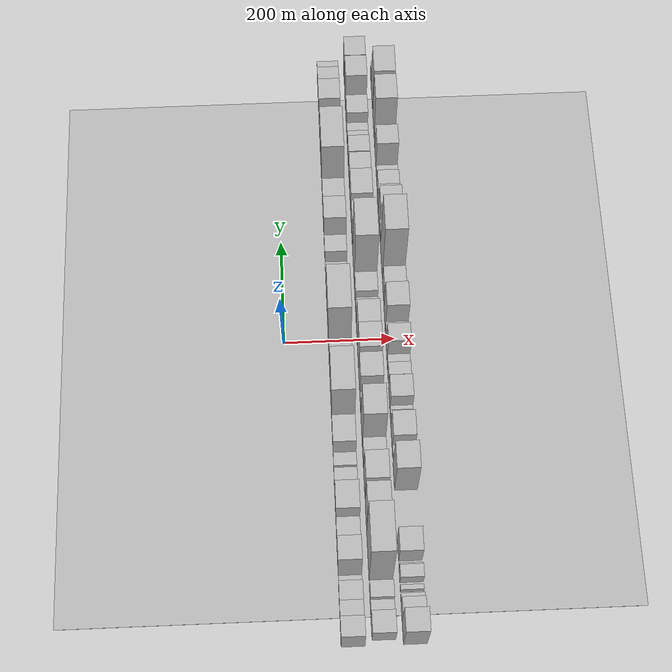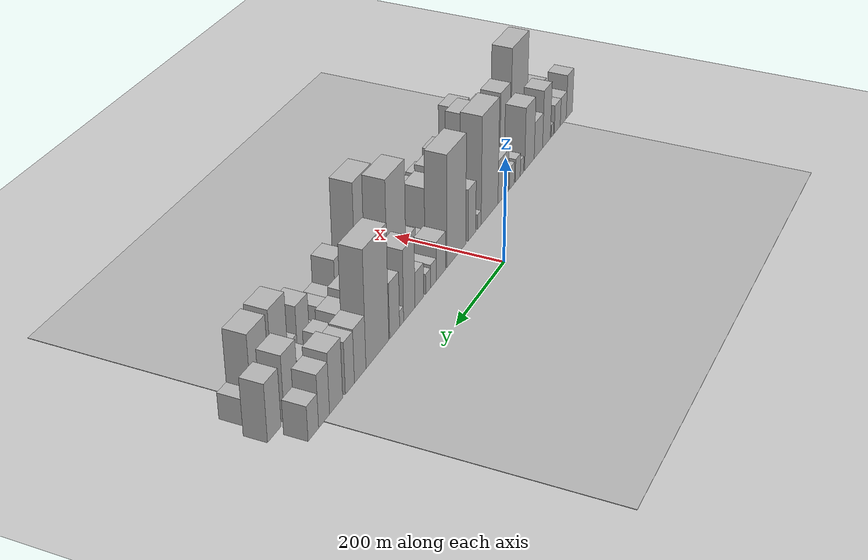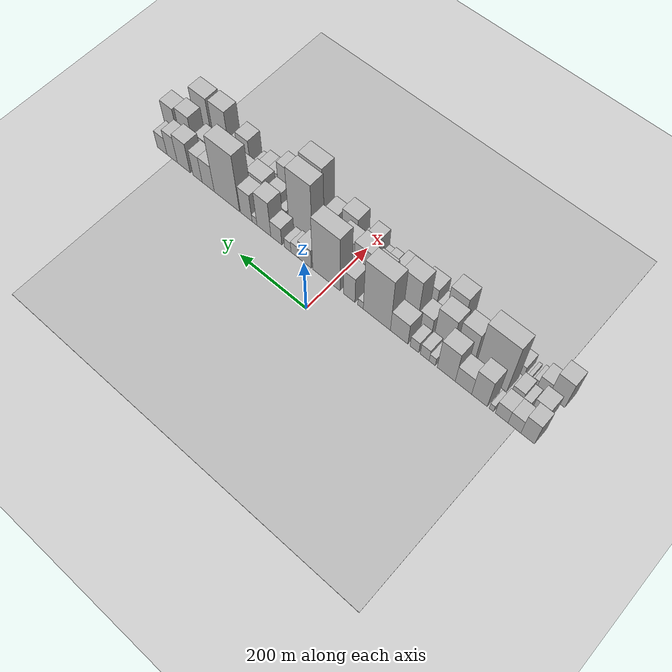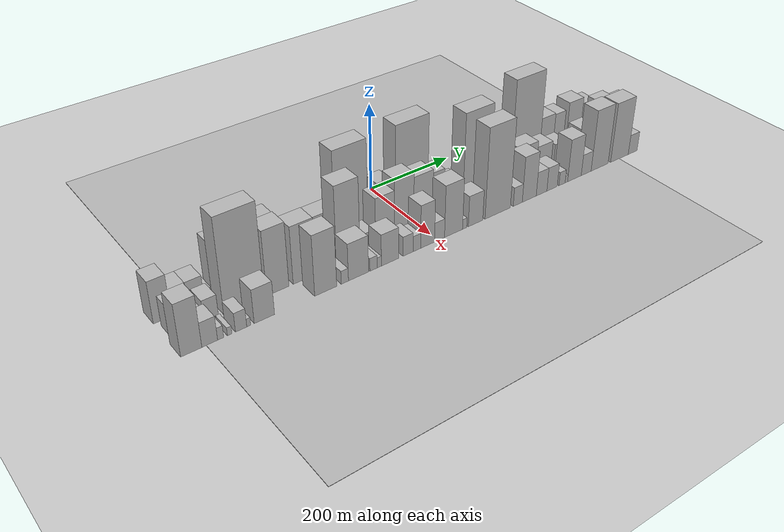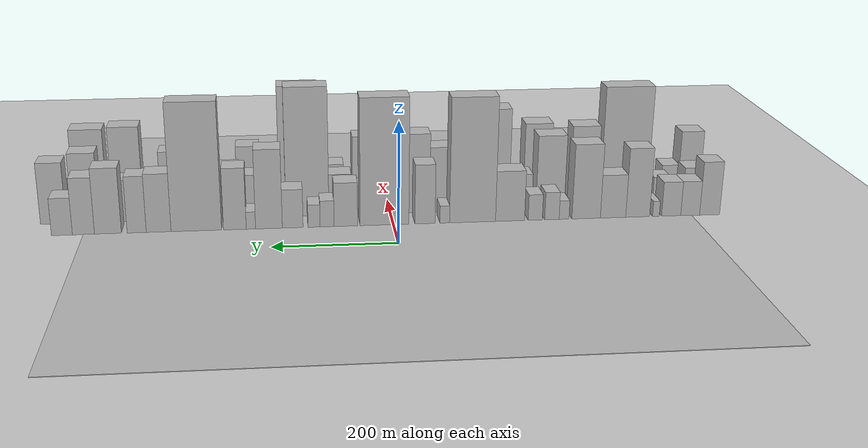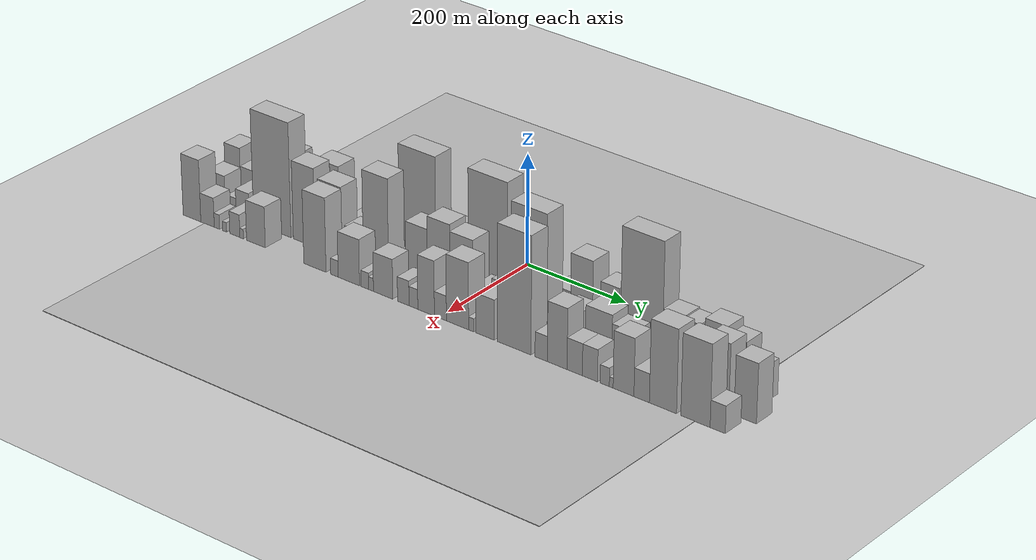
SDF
<?xml version="1.0" encoding="utf-8"?>

<sdf version="1.6">

   <world name="default">

      <gui fullscreen="0">

         <camera name="user_camera">

            <pose>-15 0 4.57585 0 0 0</pose>

            <view_controller>orbit</view_controller>

         </camera>

      </gui>

      <scene>

         <sky>

           <clouds>

             <speed>12</speed>

           </clouds>

         </sky>

         <ambient>0.4 0.4 0.4 1</ambient>

         <background>0.7 0.7 0.7 1</background>

         <shadows>1</shadows>

      </scene>

      <gravity>0 0 -9.8066</gravity>

      <magnetic_field>6e-06 2.3e-05 -4.2e-05</magnetic_field>

      <physics default="0" name="default_physics" type="ode">

         <ode>

            <solver>

               <type>quick</type>

               <iters>10</iters>

               <sor>1.0</sor>

               <use_dynamic_moi_rescaling>0</use_dynamic_moi_rescaling>

            </solver>

            <constraints>

               <cfm>0</cfm>

               <erp>0.2</erp>

               <contact_max_correcting_vel>100</contact_max_correcting_vel>

               <contact_surface_layer>0.001</contact_surface_layer>

            </constraints>

         </ode>

         <max_step_size>0.004</max_step_size>

         <real_time_factor>1</real_time_factor>

         <real_time_update_rate>250</real_time_update_rate>

      </physics>

      <light name="sun" type="directional">

         <cast_shadows>1</cast_shadows>

         <pose>0 0 10 0 0 0</pose>

         <diffuse>0.8 0.8 0.8 1</diffuse>

         <specular>0.2 0.2 0.2 1</specular>

         <attenuation>

            <range>1000</range>

            <constant>0.9</constant>

            <linear>0.01</linear>

            <quadratic>0.001</quadratic>

         </attenuation>

         <direction>-0.5 0.1 -0.9</direction>

      </light>

      <include>

         <name>ground_plane_1</name>

         <uri>model://HANNAS_ground_plane</uri>

         <pose>0 0 0  0 0 0</pose>

      </include>

      <include>

         <name>ground_plane_2</name>

         <uri>model://HANNAS_ground_plane</uri>

         <pose>100 0 0  0 0 0</pose>

      </include>

      <model name="building_1">

         <static>1</static>

         <pose frame="">100.0000 -530.8373 0 0.000000 0.000000 0.000000</pose>

         <link name="link">

            <pose frame="">0 0 46.50 0 0 0</pose>

            <collision name="collision">

               <geometry>

                  <box>

                     <size>40.0000 34.3255 93.0000</size>

                  </box>

               </geometry>

               <max_contacts>10</max_contacts>

               <surface>

                  <contact>

                     <ode/>

                  </contact>

                  <bounce/>

                  <friction>

                     <torsional>

                        <ode/>

                     </torsional>

                     <ode/>

                  </friction>

               </surface>

            </collision>

            <visual name="visual">

               <cast_shadows>0</cast_shadows>

               <geometry>

                  <box>

                     <size>40.0000 34.3255 93.0000</size>

                  </box>

               </geometry>

               <material>

                  <script>

                     <uri>model://HANNAS_wall/materials/scripts</uri>

                     <uri>model://HANNAS_wall/materials/textures</uri>

                     <name>vrc/HANNAS_wall</name>

                  </script>

               </material>

            </visual>

            <self_collide>0</self_collide>

            <enable_wind>0</enable_wind>

            <kinematic>0</kinematic>

         </link>

      </model>

      <model name="building_2">

         <static>1</static>

         <pose frame="">100.0000 -497.5036 0 0.000000 0.000000 0.000000</pose>

         <link name="link">

            <pose frame="">0 0 30.00 0 0 0</pose>

            <collision name="collision">

               <geometry>

                  <box>

                     <size>40.0000 32.3418 60.0000</size>

                  </box>

               </geometry>

               <max_contacts>10</max_contacts>

               <surface>

                  <contact>

                     <ode/>

                  </contact>

                  <bounce/>

                  <friction>

                     <torsional>

                        <ode/>

                     </torsional>

                     <ode/>

                  </friction>

               </surface>

            </collision>

            <visual name="visual">

               <cast_shadows>0</cast_shadows>

               <geometry>

                  <box>

                     <size>40.0000 32.3418 60.0000</size>

                  </box>

               </geometry>

               <material>

                  <script>

                     <uri>model://HANNAS_wall/materials/scripts</uri>

                     <uri>model://HANNAS_wall/materials/textures</uri>

                     <name>vrc/HANNAS_wall</name>

                  </script>

               </material>

            </visual>

            <self_collide>0</self_collide>

            <enable_wind>0</enable_wind>

            <kinematic>0</kinematic>

         </link>

      </model>

      <model name="building_3">

         <static>1</static>

         <pose frame="">100.0000 -465.0349 0 0.000000 0.000000 0.000000</pose>

         <link name="link">

            <pose frame="">0 0 30.00 0 0 0</pose>

            <collision name="collision">

               <geometry>

                  <box>

                     <size>40.0000 32.5957 60.0000</size>

                  </box>

               </geometry>

               <max_contacts>10</max_contacts>

               <surface>

                  <contact>

                     <ode/>

                  </contact>

                  <bounce/>

                  <friction>

                     <torsional>

                        <ode/>

                     </torsional>

                     <ode/>

                  </friction>

               </surface>

            </collision>

            <visual name="visual">

               <cast_shadows>0</cast_shadows>

               <geometry>

                  <box>

                     <size>40.0000 32.5957 60.0000</size>

                  </box>

               </geometry>

               <material>

                  <script>

                     <uri>model://HANNAS_wall/materials/scripts</uri>

                     <uri>model://HANNAS_wall/materials/textures</uri>

                     <name>vrc/HANNAS_wall</name>

                  </script>

               </material>

            </visual>

            <self_collide>0</self_collide>

            <enable_wind>0</enable_wind>

            <kinematic>0</kinematic>

         </link>

      </model>

      <model name="building_4">

         <static>1</static>

         <pose frame="">100.0000 -439.0278 0 0.000000 0.000000 0.000000</pose>

         <link name="link">

            <pose frame="">0 0 13.50 0 0 0</pose>

            <collision name="collision">

               <geometry>

                  <box>

                     <size>40.0000 11.4185 27.0000</size>

                  </box>

               </geometry>

               <max_contacts>10</max_contacts>

               <surface>

                  <contact>

                     <ode/>

                  </contact>

                  <bounce/>

                  <friction>

                     <torsional>

                        <ode/>

                     </torsional>

                     <ode/>

                  </friction>

               </surface>

            </collision>

            <visual name="visual">

               <cast_shadows>0</cast_shadows>

               <geometry>

                  <box>

                     <size>40.0000 11.4185 27.0000</size>

                  </box>

               </geometry>

               <material>

                  <script>

                     <uri>model://HANNAS_wall/materials/scripts</uri>

                     <uri>model://HANNAS_wall/materials/textures</uri>

                     <name>vrc/HANNAS_wall</name>

                  </script>

               </material>

            </visual>

            <self_collide>0</self_collide>

            <enable_wind>0</enable_wind>

            <kinematic>0</kinematic>

         </link>

      </model>

      <model name="building_5">

         <static>1</static>

         <pose frame="">100.0000 -407.9759 0 0.000000 0.000000 0.000000</pose>

         <link name="link">

            <pose frame="">0 0 60.00 0 0 0</pose>

            <collision name="collision">

               <geometry>

                  <box>

                     <size>40.0000 40.6853 120.0000</size>

                  </box>

               </geometry>

               <max_contacts>10</max_contacts>

               <surface>

                  <contact>

                     <ode/>

                  </contact>

                  <bounce/>

                  <friction>

                     <torsional>

                        <ode/>

                     </torsional>

                     <ode/>

                  </friction>

               </surface>

            </collision>

            <visual name="visual">

               <cast_shadows>0</cast_shadows>

               <geometry>

                  <box>

                     <size>40.0000 40.6853 120.0000</size>

                  </box>

               </geometry>

               <material>

                  <script>

                     <uri>model://HANNAS_wall/materials/scripts</uri>

                     <uri>model://HANNAS_wall/materials/textures</uri>

                     <name>vrc/HANNAS_wall</name>

                  </script>

               </material>

            </visual>

            <self_collide>0</self_collide>

            <enable_wind>0</enable_wind>

            <kinematic>0</kinematic>

         </link>

      </model>

      <model name="building_6">

         <static>1</static>

         <pose frame="">100.0000 -366.1311 0 0.000000 0.000000 0.000000</pose>

         <link name="link">

            <pose frame="">0 0 37.50 0 0 0</pose>

            <collision name="collision">

               <geometry>

                  <box>

                     <size>40.0000 43.0041 75.0000</size>

                  </box>

               </geometry>

               <max_contacts>10</max_contacts>

               <surface>

                  <contact>

                     <ode/>

                  </contact>

                  <bounce/>

                  <friction>

                     <torsional>

                        <ode/>

                     </torsional>

                     <ode/>

                  </friction>

               </surface>

            </collision>

            <visual name="visual">

               <cast_shadows>0</cast_shadows>

               <geometry>

                  <box>

                     <size>40.0000 43.0041 75.0000</size>

                  </box>

               </geometry>

               <material>

                  <script>

                     <uri>model://HANNAS_wall/materials/scripts</uri>

                     <uri>model://HANNAS_wall/materials/textures</uri>

                     <name>vrc/HANNAS_wall</name>

                  </script>

               </material>

            </visual>

            <self_collide>0</self_collide>

            <enable_wind>0</enable_wind>

            <kinematic>0</kinematic>

         </link>

      </model>

      <model name="building_7">

         <static>1</static>

         <pose frame="">100.0000 -320.7055 0 0.000000 0.000000 0.000000</pose>

         <link name="link">

            <pose frame="">0 0 64.50 0 0 0</pose>

            <collision name="collision">

               <geometry>

                  <box>

                     <size>40.0000 47.8472 129.0000</size>

                  </box>

               </geometry>

               <max_contacts>10</max_contacts>

               <surface>

                  <contact>

                     <ode/>

                  </contact>

                  <bounce/>

                  <friction>

                     <torsional>

                        <ode/>

                     </torsional>

                     <ode/>

                  </friction>

               </surface>

            </collision>

            <visual name="visual">

               <cast_shadows>0</cast_shadows>

               <geometry>

                  <box>

                     <size>40.0000 47.8472 129.0000</size>

                  </box>

               </geometry>

               <material>

                  <script>

                     <uri>model://HANNAS_wall/materials/scripts</uri>

                     <uri>model://HANNAS_wall/materials/textures</uri>

                     <name>vrc/HANNAS_wall</name>

                  </script>

               </material>

            </visual>

            <self_collide>0</self_collide>

            <enable_wind>0</enable_wind>

            <kinematic>0</kinematic>

         </link>

      </model>

      <model name="building_8">

         <static>1</static>

         <pose frame="">100.0000 -283.4614 0 0.000000 0.000000 0.000000</pose>

         <link name="link">

            <pose frame="">0 0 16.50 0 0 0</pose>

            <collision name="collision">

               <geometry>

                  <box>

                     <size>40.0000 16.6410 33.0000</size>

                  </box>

               </geometry>

               <max_contacts>10</max_contacts>

               <surface>

                  <contact>

                     <ode/>

                  </contact>

                  <bounce/>

                  <friction>

                     <torsional>

                        <ode/>

                     </torsional>

                     <ode/>

                  </friction>

               </surface>

            </collision>

            <visual name="visual">

               <cast_shadows>0</cast_shadows>

               <geometry>

                  <box>

                     <size>40.0000 16.6410 33.0000</size>

                  </box>

               </geometry>

               <material>

                  <script>

                     <uri>model://HANNAS_wall/materials/scripts</uri>

                     <uri>model://HANNAS_wall/materials/textures</uri>

                     <name>vrc/HANNAS_wall</name>

                  </script>

               </material>

            </visual>

            <self_collide>0</self_collide>

            <enable_wind>0</enable_wind>

            <kinematic>0</kinematic>

         </link>

      </model>

      <model name="building_9">

         <static>1</static>

         <pose frame="">100.0000 -263.0421 0 0.000000 0.000000 0.000000</pose>

         <link name="link">

            <pose frame="">0 0 24.00 0 0 0</pose>

            <collision name="collision">

               <geometry>

                  <box>

                     <size>40.0000 24.1975 48.0000</size>

                  </box>

               </geometry>

               <max_contacts>10</max_contacts>

               <surface>

                  <contact>

                     <ode/>

                  </contact>

                  <bounce/>

                  <friction>

                     <torsional>

                        <ode/>

                     </torsional>

                     <ode/>

                  </friction>

               </surface>

            </collision>

            <visual name="visual">

               <cast_shadows>0</cast_shadows>

               <geometry>

                  <box>

                     <size>40.0000 24.1975 48.0000</size>

                  </box>

               </geometry>

               <material>

                  <script>

                     <uri>model://HANNAS_wall/materials/scripts</uri>

                     <uri>model://HANNAS_wall/materials/textures</uri>

                     <name>vrc/HANNAS_wall</name>

                  </script>

               </material>

            </visual>

            <self_collide>0</self_collide>

            <enable_wind>0</enable_wind>

            <kinematic>0</kinematic>

         </link>

      </model>

      <model name="building_10">

         <static>1</static>

         <pose frame="">100.0000 -235.0637 0 0.000000 0.000000 0.000000</pose>

         <link name="link">

            <pose frame="">0 0 22.50 0 0 0</pose>

            <collision name="collision">

               <geometry>

                  <box>

                     <size>40.0000 23.7592 45.0000</size>

                  </box>

               </geometry>

               <max_contacts>10</max_contacts>

               <surface>

                  <contact>

                     <ode/>

                  </contact>

                  <bounce/>

                  <friction>

                     <torsional>

                        <ode/>

                     </torsional>

                     <ode/>

                  </friction>

               </surface>

            </collision>

            <visual name="visual">

               <cast_shadows>0</cast_shadows>

               <geometry>

                  <box>

                     <size>40.0000 23.7592 45.0000</size>

                  </box>

               </geometry>

               <material>

                  <script>

                     <uri>model://HANNAS_wall/materials/scripts</uri>

                     <uri>model://HANNAS_wall/materials/textures</uri>

                     <name>vrc/HANNAS_wall</name>

                  </script>

               </material>

            </visual>

            <self_collide>0</self_collide>

            <enable_wind>0</enable_wind>

            <kinematic>0</kinematic>

         </link>

      </model>

      <model name="building_11">

         <static>1</static>

         <pose frame="">100.0000 -192.9801 0 0.000000 0.000000 0.000000</pose>

         <link name="link">

            <pose frame="">0 0 43.50 0 0 0</pose>

            <collision name="collision">

               <geometry>

                  <box>

                     <size>40.0000 48.4080 87.0000</size>

                  </box>

               </geometry>

               <max_contacts>10</max_contacts>

               <surface>

                  <contact>

                     <ode/>

                  </contact>

                  <bounce/>

                  <friction>

                     <torsional>

                        <ode/>

                     </torsional>

                     <ode/>

                  </friction>

               </surface>

            </collision>

            <visual name="visual">

               <cast_shadows>0</cast_shadows>

               <geometry>

                  <box>

                     <size>40.0000 48.4080 87.0000</size>

                  </box>

               </geometry>

               <material>

                  <script>

                     <uri>model://HANNAS_wall/materials/scripts</uri>

                     <uri>model://HANNAS_wall/materials/textures</uri>

                     <name>vrc/HANNAS_wall</name>

                  </script>

               </material>

            </visual>

            <self_collide>0</self_collide>

            <enable_wind>0</enable_wind>

            <kinematic>0</kinematic>

         </link>

      </model>

      <model name="building_12">

         <static>1</static>

         <pose frame="">100.0000 -130.5440 0 0.000000 0.000000 0.000000</pose>

         <link name="link">

            <pose frame="">0 0 106.50 0 0 0</pose>

            <collision name="collision">

               <geometry>

                  <box>

                     <size>40.0000 76.4643 213.0000</size>

                  </box>

               </geometry>

               <max_contacts>10</max_contacts>

               <surface>

                  <contact>

                     <ode/>

                  </contact>

                  <bounce/>

                  <friction>

                     <torsional>

                        <ode/>

                     </torsional>

                     <ode/>

                  </friction>

               </surface>

            </collision>

            <visual name="visual">

               <cast_shadows>0</cast_shadows>

               <geometry>

                  <box>

                     <size>40.0000 76.4643 213.0000</size>

                  </box>

               </geometry>

               <material>

                  <script>

                     <uri>model://HANNAS_wall/materials/scripts</uri>

                     <uri>model://HANNAS_wall/materials/textures</uri>

                     <name>vrc/HANNAS_wall</name>

                  </script>

               </material>

            </visual>

            <self_collide>0</self_collide>

            <enable_wind>0</enable_wind>

            <kinematic>0</kinematic>

         </link>

      </model>

      <model name="building_13">

         <static>1</static>

         <pose frame="">100.0000 -84.3741 0 0.000000 0.000000 0.000000</pose>

         <link name="link">

            <pose frame="">0 0 15.00 0 0 0</pose>

            <collision name="collision">

               <geometry>

                  <box>

                     <size>40.0000 15.8754 30.0000</size>

                  </box>

               </geometry>

               <max_contacts>10</max_contacts>

               <surface>

                  <contact>

                     <ode/>

                  </contact>

                  <bounce/>

                  <friction>

                     <torsional>

                        <ode/>

                     </torsional>

                     <ode/>

                  </friction>

               </surface>

            </collision>

            <visual name="visual">

               <cast_shadows>0</cast_shadows>

               <geometry>

                  <box>

                     <size>40.0000 15.8754 30.0000</size>

                  </box>

               </geometry>

               <material>

                  <script>

                     <uri>model://HANNAS_wall/materials/scripts</uri>

                     <uri>model://HANNAS_wall/materials/textures</uri>

                     <name>vrc/HANNAS_wall</name>

                  </script>

               </material>

            </visual>

            <self_collide>0</self_collide>

            <enable_wind>0</enable_wind>

            <kinematic>0</kinematic>

         </link>

      </model>

      <model name="building_14">

         <static>1</static>

         <pose frame="">100.0000 -51.7980 0 0.000000 0.000000 0.000000</pose>

         <link name="link">

            <pose frame="">0 0 51.00 0 0 0</pose>

            <collision name="collision">

               <geometry>

                  <box>

                     <size>40.0000 33.2770 102.0000</size>

                  </box>

               </geometry>

               <max_contacts>10</max_contacts>

               <surface>

                  <contact>

                     <ode/>

                  </contact>

                  <bounce/>

                  <friction>

                     <torsional>

                        <ode/>

                     </torsional>

                     <ode/>

                  </friction>

               </surface>

            </collision>

            <visual name="visual">

               <cast_shadows>0</cast_shadows>

               <geometry>

                  <box>

                     <size>40.0000 33.2770 102.0000</size>

                  </box>

               </geometry>

               <material>

                  <script>

                     <uri>model://HANNAS_wall/materials/scripts</uri>

                     <uri>model://HANNAS_wall/materials/textures</uri>

                     <name>vrc/HANNAS_wall</name>

                  </script>

               </material>

            </visual>

            <self_collide>0</self_collide>

            <enable_wind>0</enable_wind>

            <kinematic>0</kinematic>

         </link>

      </model>

      <model name="building_15">

         <static>1</static>

         <pose frame="">100.0000 14.8957 0 0.000000 0.000000 0.000000</pose>

         <link name="link">

            <pose frame="">0 0 108.00 0 0 0</pose>

            <collision name="collision">

               <geometry>

                  <box>

                     <size>40.0000 80.1104 216.0000</size>

                  </box>

               </geometry>

               <max_contacts>10</max_contacts>

               <surface>

                  <contact>

                     <ode/>

                  </contact>

                  <bounce/>

                  <friction>

                     <torsional>

                        <ode/>

                     </torsional>

                     <ode/>

                  </friction>

               </surface>

            </collision>

            <visual name="visual">

               <cast_shadows>0</cast_shadows>

               <geometry>

                  <box>

                     <size>40.0000 80.1104 216.0000</size>

                  </box>

               </geometry>

               <material>

                  <script>

                     <uri>model://HANNAS_wall/materials/scripts</uri>

                     <uri>model://HANNAS_wall/materials/textures</uri>

                     <name>vrc/HANNAS_wall</name>

                  </script>

               </material>

            </visual>

            <self_collide>0</self_collide>

            <enable_wind>0</enable_wind>

            <kinematic>0</kinematic>

         </link>

      </model>

      <model name="building_16">

         <static>1</static>

         <pose frame="">100.0000 78.2823 0 0.000000 0.000000 0.000000</pose>

         <link name="link">

            <pose frame="">0 0 37.50 0 0 0</pose>

            <collision name="collision">

               <geometry>

                  <box>

                     <size>40.0000 38.6628 75.0000</size>

                  </box>

               </geometry>

               <max_contacts>10</max_contacts>

               <surface>

                  <contact>

                     <ode/>

                  </contact>

                  <bounce/>

                  <friction>

                     <torsional>

                        <ode/>

                     </torsional>

                     <ode/>

                  </friction>

               </surface>

            </collision>

            <visual name="visual">

               <cast_shadows>0</cast_shadows>

               <geometry>

                  <box>

                     <size>40.0000 38.6628 75.0000</size>

                  </box>

               </geometry>

               <material>

                  <script>

                     <uri>model://HANNAS_wall/materials/scripts</uri>

                     <uri>model://HANNAS_wall/materials/textures</uri>

                     <name>vrc/HANNAS_wall</name>

                  </script>

               </material>

            </visual>

            <self_collide>0</self_collide>

            <enable_wind>0</enable_wind>

            <kinematic>0</kinematic>

         </link>

      </model>

      <model name="building_17">

         <static>1</static>

         <pose frame="">100.0000 108.9480 0 0.000000 0.000000 0.000000</pose>

         <link name="link">

            <pose frame="">0 0 22.50 0 0 0</pose>

            <collision name="collision">

               <geometry>

                  <box>

                     <size>40.0000 22.6685 45.0000</size>

                  </box>

               </geometry>

               <max_contacts>10</max_contacts>

               <surface>

                  <contact>

                     <ode/>

                  </contact>

                  <bounce/>

                  <friction>

                     <torsional>

                        <ode/>

                     </torsional>

                     <ode/>

                  </friction>

               </surface>

            </collision>

            <visual name="visual">

               <cast_shadows>0</cast_shadows>

               <geometry>

                  <box>

                     <size>40.0000 22.6685 45.0000</size>

                  </box>

               </geometry>

               <material>

                  <script>

                     <uri>model://HANNAS_wall/materials/scripts</uri>

                     <uri>model://HANNAS_wall/materials/textures</uri>

                     <name>vrc/HANNAS_wall</name>

                  </script>

               </material>

            </visual>

            <self_collide>0</self_collide>

            <enable_wind>0</enable_wind>

            <kinematic>0</kinematic>

         </link>

      </model>

      <model name="building_18">

         <static>1</static>

         <pose frame="">100.0000 130.1563 0 0.000000 0.000000 0.000000</pose>

         <link name="link">

            <pose frame="">0 0 19.50 0 0 0</pose>

            <collision name="collision">

               <geometry>

                  <box>

                     <size>40.0000 19.7481 39.0000</size>

                  </box>

               </geometry>

               <max_contacts>10</max_contacts>

               <surface>

                  <contact>

                     <ode/>

                  </contact>

                  <bounce/>

                  <friction>

                     <torsional>

                        <ode/>

                     </torsional>

                     <ode/>

                  </friction>

               </surface>

            </collision>

            <visual name="visual">

               <cast_shadows>0</cast_shadows>

               <geometry>

                  <box>

                     <size>40.0000 19.7481 39.0000</size>

                  </box>

               </geometry>

               <material>

                  <script>

                     <uri>model://HANNAS_wall/materials/scripts</uri>

                     <uri>model://HANNAS_wall/materials/textures</uri>

                     <name>vrc/HANNAS_wall</name>

                  </script>

               </material>

            </visual>

            <self_collide>0</self_collide>

            <enable_wind>0</enable_wind>

            <kinematic>0</kinematic>

         </link>

      </model>

      <model name="building_19">

         <static>1</static>

         <pose frame="">100.0000 164.8471 0 0.000000 0.000000 0.000000</pose>

         <link name="link">

            <pose frame="">0 0 33.00 0 0 0</pose>

            <collision name="collision">

               <geometry>

                  <box>

                     <size>40.0000 33.6333 66.0000</size>

                  </box>

               </geometry>

               <max_contacts>10</max_contacts>

               <surface>

                  <contact>

                     <ode/>

                  </contact>

                  <bounce/>

                  <friction>

                     <torsional>

                        <ode/>

                     </torsional>

                     <ode/>

                  </friction>

               </surface>

            </collision>

            <visual name="visual">

               <cast_shadows>0</cast_shadows>

               <geometry>

                  <box>

                     <size>40.0000 33.6333 66.0000</size>

                  </box>

               </geometry>

               <material>

                  <script>

                     <uri>model://HANNAS_wall/materials/scripts</uri>

                     <uri>model://HANNAS_wall/materials/textures</uri>

                     <name>vrc/HANNAS_wall</name>

                  </script>

               </material>

            </visual>

            <self_collide>0</self_collide>

            <enable_wind>0</enable_wind>

            <kinematic>0</kinematic>

         </link>

      </model>

      <model name="building_20">

         <static>1</static>

         <pose frame="">100.0000 203.2782 0 0.000000 0.000000 0.000000</pose>

         <link name="link">

            <pose frame="">0 0 67.50 0 0 0</pose>

            <collision name="collision">

               <geometry>

                  <box>

                     <size>40.0000 43.2290 135.0000</size>

                  </box>

               </geometry>

               <max_contacts>10</max_contacts>

               <surface>

                  <contact>

                     <ode/>

                  </contact>

                  <bounce/>

                  <friction>

                     <torsional>

                        <ode/>

                     </torsional>

                     <ode/>

                  </friction>

               </surface>

            </collision>

            <visual name="visual">

               <cast_shadows>0</cast_shadows>

               <geometry>

                  <box>

                     <size>40.0000 43.2290 135.0000</size>

                  </box>

               </geometry>

               <material>

                  <script>

                     <uri>model://HANNAS_wall/materials/scripts</uri>

                     <uri>model://HANNAS_wall/materials/textures</uri>

                     <name>vrc/HANNAS_wall</name>

                  </script>

               </material>

            </visual>

            <self_collide>0</self_collide>

            <enable_wind>0</enable_wind>

            <kinematic>0</kinematic>

         </link>

      </model>

      <model name="building_21">

         <static>1</static>

         <pose frame="">100.0000 232.4542 0 0.000000 0.000000 0.000000</pose>

         <link name="link">

            <pose frame="">0 0 15.00 0 0 0</pose>

            <collision name="collision">

               <geometry>

                  <box>

                     <size>40.0000 15.1230 30.0000</size>

                  </box>

               </geometry>

               <max_contacts>10</max_contacts>

               <surface>

                  <contact>

                     <ode/>

                  </contact>

                  <bounce/>

                  <friction>

                     <torsional>

                        <ode/>

                     </torsional>

                     <ode/>

                  </friction>

               </surface>

            </collision>

            <visual name="visual">

               <cast_shadows>0</cast_shadows>

               <geometry>

                  <box>

                     <size>40.0000 15.1230 30.0000</size>

                  </box>

               </geometry>

               <material>

                  <script>

                     <uri>model://HANNAS_wall/materials/scripts</uri>

                     <uri>model://HANNAS_wall/materials/textures</uri>

                     <name>vrc/HANNAS_wall</name>

                  </script>

               </material>

            </visual>

            <self_collide>0</self_collide>

            <enable_wind>0</enable_wind>

            <kinematic>0</kinematic>

         </link>

      </model>

      <model name="building_22">

         <static>1</static>

         <pose frame="">100.0000 258.2992 0 0.000000 0.000000 0.000000</pose>

         <link name="link">

            <pose frame="">0 0 52.50 0 0 0</pose>

            <collision name="collision">

               <geometry>

                  <box>

                     <size>40.0000 36.5669 105.0000</size>

                  </box>

               </geometry>

               <max_contacts>10</max_contacts>

               <surface>

                  <contact>

                     <ode/>

                  </contact>

                  <bounce/>

                  <friction>

                     <torsional>

                        <ode/>

                     </torsional>

                     <ode/>

                  </friction>

               </surface>

            </collision>

            <visual name="visual">

               <cast_shadows>0</cast_shadows>

               <geometry>

                  <box>

                     <size>40.0000 36.5669 105.0000</size>

                  </box>

               </geometry>

               <material>

                  <script>

                     <uri>model://HANNAS_wall/materials/scripts</uri>

                     <uri>model://HANNAS_wall/materials/textures</uri>

                     <name>vrc/HANNAS_wall</name>

                  </script>

               </material>

            </visual>

            <self_collide>0</self_collide>

            <enable_wind>0</enable_wind>

            <kinematic>0</kinematic>

         </link>

      </model>

      <model name="building_23">

         <static>1</static>

         <pose frame="">100.0000 320.1064 0 0.000000 0.000000 0.000000</pose>

         <link name="link">

            <pose frame="">0 0 108.00 0 0 0</pose>

            <collision name="collision">

               <geometry>

                  <box>

                     <size>40.0000 81.0476 216.0000</size>

                  </box>

               </geometry>

               <max_contacts>10</max_contacts>

               <surface>

                  <contact>

                     <ode/>

                  </contact>

                  <bounce/>

                  <friction>

                     <torsional>

                        <ode/>

                     </torsional>

                     <ode/>

                  </friction>

               </surface>

            </collision>

            <visual name="visual">

               <cast_shadows>0</cast_shadows>

               <geometry>

                  <box>

                     <size>40.0000 81.0476 216.0000</size>

                  </box>

               </geometry>

               <material>

                  <script>

                     <uri>model://HANNAS_wall/materials/scripts</uri>

                     <uri>model://HANNAS_wall/materials/textures</uri>

                     <name>vrc/HANNAS_wall</name>

                  </script>

               </material>

            </visual>

            <self_collide>0</self_collide>

            <enable_wind>0</enable_wind>

            <kinematic>0</kinematic>

         </link>

      </model>

      <model name="building_24">

         <static>1</static>

         <pose frame="">100.0000 380.3925 0 0.000000 0.000000 0.000000</pose>

         <link name="link">

            <pose frame="">0 0 49.50 0 0 0</pose>

            <collision name="collision">

               <geometry>

                  <box>

                     <size>40.0000 39.5247 99.0000</size>

                  </box>

               </geometry>

               <max_contacts>10</max_contacts>

               <surface>

                  <contact>

                     <ode/>

                  </contact>

                  <bounce/>

                  <friction>

                     <torsional>

                        <ode/>

                     </torsional>

                     <ode/>

                  </friction>

               </surface>

            </collision>

            <visual name="visual">

               <cast_shadows>0</cast_shadows>

               <geometry>

                  <box>

                     <size>40.0000 39.5247 99.0000</size>

                  </box>

               </geometry>

               <material>

                  <script>

                     <uri>model://HANNAS_wall/materials/scripts</uri>

                     <uri>model://HANNAS_wall/materials/textures</uri>

                     <name>vrc/HANNAS_wall</name>

                  </script>

               </material>

            </visual>

            <self_collide>0</self_collide>

            <enable_wind>0</enable_wind>

            <kinematic>0</kinematic>

         </link>

      </model>

      <model name="building_25">

         <static>1</static>

         <pose frame="">100.0000 415.3816 0 0.000000 0.000000 0.000000</pose>

         <link name="link">

            <pose frame="">0 0 48.00 0 0 0</pose>

            <collision name="collision">

               <geometry>

                  <box>

                     <size>40.0000 30.4535 96.0000</size>

                  </box>

               </geometry>

               <max_contacts>10</max_contacts>

               <surface>

                  <contact>

                     <ode/>

                  </contact>

                  <bounce/>

                  <friction>

                     <torsional>

                        <ode/>

                     </torsional>

                     <ode/>

                  </friction>

               </surface>

            </collision>

            <visual name="visual">

               <cast_shadows>0</cast_shadows>

               <geometry>

                  <box>

                     <size>40.0000 30.4535 96.0000</size>

                  </box>

               </geometry>

               <material>

                  <script>

                     <uri>model://HANNAS_wall/materials/scripts</uri>

                     <uri>model://HANNAS_wall/materials/textures</uri>

                     <name>vrc/HANNAS_wall</name>

                  </script>

               </material>

            </visual>

            <self_collide>0</self_collide>

            <enable_wind>0</enable_wind>

            <kinematic>0</kinematic>

         </link>

      </model>

      <model name="building_26">

         <static>1</static>

         <pose frame="">100.0000 460.9299 0 0.000000 0.000000 0.000000</pose>

         <link name="link">

            <pose frame="">0 0 55.50 0 0 0</pose>

            <collision name="collision">

               <geometry>

                  <box>

                     <size>40.0000 42.6431 111.0000</size>

                  </box>

               </geometry>

               <max_contacts>10</max_contacts>

               <surface>

                  <contact>

                     <ode/>

                  </contact>

                  <bounce/>

                  <friction>

                     <torsional>

                        <ode/>

                     </torsional>

                     <ode/>

                  </friction>

               </surface>

            </collision>

            <visual name="visual">

               <cast_shadows>0</cast_shadows>

               <geometry>

                  <box>

                     <size>40.0000 42.6431 111.0000</size>

                  </box>

               </geometry>

               <material>

                  <script>

                     <uri>model://HANNAS_wall/materials/scripts</uri>

                     <uri>model://HANNAS_wall/materials/textures</uri>

                     <name>vrc/HANNAS_wall</name>

                  </script>

               </material>

            </visual>

            <self_collide>0</self_collide>

            <enable_wind>0</enable_wind>

            <kinematic>0</kinematic>

         </link>

      </model>

      <model name="building_27">

         <static>1</static>

         <pose frame="">100.0000 499.7047 0 0.000000 0.000000 0.000000</pose>

         <link name="link">

            <pose frame="">0 0 48.00 0 0 0</pose>

            <collision name="collision">

               <geometry>

                  <box>

                     <size>40.0000 34.9063 96.0000</size>

                  </box>

               </geometry>

               <max_contacts>10</max_contacts>

               <surface>

                  <contact>

                     <ode/>

                  </contact>

                  <bounce/>

                  <friction>

                     <torsional>

                        <ode/>

                     </torsional>

                     <ode/>

                  </friction>

               </surface>

            </collision>

            <visual name="visual">

               <cast_shadows>0</cast_shadows>

               <geometry>

                  <box>

                     <size>40.0000 34.9063 96.0000</size>

                  </box>

               </geometry>

               <material>

                  <script>

                     <uri>model://HANNAS_wall/materials/scripts</uri>

                     <uri>model://HANNAS_wall/materials/textures</uri>

                     <name>vrc/HANNAS_wall</name>

                  </script>

               </material>

            </visual>

            <self_collide>0</self_collide>

            <enable_wind>0</enable_wind>

            <kinematic>0</kinematic>

         </link>

      </model>

      <model name="building_28">

         <static>1</static>

         <pose frame="">100.0000 533.6708 0 0.000000 0.000000 0.000000</pose>

         <link name="link">

            <pose frame="">0 0 31.50 0 0 0</pose>

            <collision name="collision">

               <geometry>

                  <box>

                     <size>40.0000 33.0259 63.0000</size>

                  </box>

               </geometry>

               <max_contacts>10</max_contacts>

               <surface>

                  <contact>

                     <ode/>

                  </contact>

                  <bounce/>

                  <friction>

                     <torsional>

                        <ode/>

                     </torsional>

                     <ode/>

                  </friction>

               </surface>

            </collision>

            <visual name="visual">

               <cast_shadows>0</cast_shadows>

               <geometry>

                  <box>

                     <size>40.0000 33.0259 63.0000</size>

                  </box>

               </geometry>

               <material>

                  <script>

                     <uri>model://HANNAS_wall/materials/scripts</uri>

                     <uri>model://HANNAS_wall/materials/textures</uri>

                     <name>vrc/HANNAS_wall</name>

                  </script>

               </material>

            </visual>

            <self_collide>0</self_collide>

            <enable_wind>0</enable_wind>

            <kinematic>0</kinematic>

         </link>

      </model>

      <model name="building_29">

         <static>1</static>

         <pose frame="">152.0000 -520.1196 0 0.000000 0.000000 0.000000</pose>

         <link name="link">

            <pose frame="">0 0 33.00 0 0 0</pose>

            <collision name="collision">

               <geometry>

                  <box>

                     <size>40.0000 37.7607 66.0000</size>

                  </box>

               </geometry>

               <max_contacts>10</max_contacts>

               <surface>

                  <contact>

                     <ode/>

                  </contact>

                  <bounce/>

                  <friction>

                     <torsional>

                        <ode/>

                     </torsional>

                     <ode/>

                  </friction>

               </surface>

            </collision>

            <visual name="visual">

               <cast_shadows>0</cast_shadows>

               <geometry>

                  <box>

                     <size>40.0000 37.7607 66.0000</size>

                  </box>

               </geometry>

               <material>

                  <script>

                     <uri>model://HANNAS_wall/materials/scripts</uri>

                     <uri>model://HANNAS_wall/materials/textures</uri>

                     <name>vrc/HANNAS_wall</name>

                  </script>

               </material>

            </visual>

            <self_collide>0</self_collide>

            <enable_wind>0</enable_wind>

            <kinematic>0</kinematic>

         </link>

      </model>

      <model name="building_30">

         <static>1</static>

         <pose frame="">152.0000 -486.7335 0 0.000000 0.000000 0.000000</pose>

         <link name="link">

            <pose frame="">0 0 16.50 0 0 0</pose>

            <collision name="collision">

               <geometry>

                  <box>

                     <size>40.0000 19.0117 33.0000</size>

                  </box>

               </geometry>

               <max_contacts>10</max_contacts>

               <surface>

                  <contact>

                     <ode/>

                  </contact>

                  <bounce/>

                  <friction>

                     <torsional>

                        <ode/>

                     </torsional>

                     <ode/>

                  </friction>

               </surface>

            </collision>

            <visual name="visual">

               <cast_shadows>0</cast_shadows>

               <geometry>

                  <box>

                     <size>40.0000 19.0117 33.0000</size>

                  </box>

               </geometry>

               <material>

                  <script>

                     <uri>model://HANNAS_wall/materials/scripts</uri>

                     <uri>model://HANNAS_wall/materials/textures</uri>

                     <name>vrc/HANNAS_wall</name>

                  </script>

               </material>

            </visual>

            <self_collide>0</self_collide>

            <enable_wind>0</enable_wind>

            <kinematic>0</kinematic>

         </link>

      </model>

      <model name="building_31">

         <static>1</static>

         <pose frame="">152.0000 -462.7647 0 0.000000 0.000000 0.000000</pose>

         <link name="link">

            <pose frame="">0 0 25.50 0 0 0</pose>

            <collision name="collision">

               <geometry>

                  <box>

                     <size>40.0000 28.9259 51.0000</size>

                  </box>

               </geometry>

               <max_contacts>10</max_contacts>

               <surface>

                  <contact>

                     <ode/>

                  </contact>

                  <bounce/>

                  <friction>

                     <torsional>

                        <ode/>

                     </torsional>

                     <ode/>

                  </friction>

               </surface>

            </collision>

            <visual name="visual">

               <cast_shadows>0</cast_shadows>

               <geometry>

                  <box>

                     <size>40.0000 28.9259 51.0000</size>

                  </box>

               </geometry>

               <material>

                  <script>

                     <uri>model://HANNAS_wall/materials/scripts</uri>

                     <uri>model://HANNAS_wall/materials/textures</uri>

                     <name>vrc/HANNAS_wall</name>

                  </script>

               </material>

            </visual>

            <self_collide>0</self_collide>

            <enable_wind>0</enable_wind>

            <kinematic>0</kinematic>

         </link>

      </model>

      <model name="building_32">

         <static>1</static>

         <pose frame="">152.0000 -397.3396 0 0.000000 0.000000 0.000000</pose>

         <link name="link">

            <pose frame="">0 0 105.00 0 0 0</pose>

            <collision name="collision">

               <geometry>

                  <box>

                     <size>40.0000 81.9243 210.0000</size>

                  </box>

               </geometry>

               <max_contacts>10</max_contacts>

               <surface>

                  <contact>

                     <ode/>

                  </contact>

                  <bounce/>

                  <friction>

                     <torsional>

                        <ode/>

                     </torsional>

                     <ode/>

                  </friction>

               </surface>

            </collision>

            <visual name="visual">

               <cast_shadows>0</cast_shadows>

               <geometry>

                  <box>

                     <size>40.0000 81.9243 210.0000</size>

                  </box>

               </geometry>

               <material>

                  <script>

                     <uri>model://HANNAS_wall/materials/scripts</uri>

                     <uri>model://HANNAS_wall/materials/textures</uri>

                     <name>vrc/HANNAS_wall</name>

                  </script>

               </material>

            </visual>

            <self_collide>0</self_collide>

            <enable_wind>0</enable_wind>

            <kinematic>0</kinematic>

         </link>

      </model>

      <model name="building_33">

         <static>1</static>

         <pose frame="">152.0000 -327.9991 0 0.000000 0.000000 0.000000</pose>

         <link name="link">

            <pose frame="">0 0 72.00 0 0 0</pose>

            <collision name="collision">

               <geometry>

                  <box>

                     <size>40.0000 46.7567 144.0000</size>

                  </box>

               </geometry>

               <max_contacts>10</max_contacts>

               <surface>

                  <contact>

                     <ode/>

                  </contact>

                  <bounce/>

                  <friction>

                     <torsional>

                        <ode/>

                     </torsional>

                     <ode/>

                  </friction>

               </surface>

            </collision>

            <visual name="visual">

               <cast_shadows>0</cast_shadows>

               <geometry>

                  <box>

                     <size>40.0000 46.7567 144.0000</size>

                  </box>

               </geometry>

               <material>

                  <script>

                     <uri>model://HANNAS_wall/materials/scripts</uri>

                     <uri>model://HANNAS_wall/materials/textures</uri>

                     <name>vrc/HANNAS_wall</name>

                  </script>

               </material>

            </visual>

            <self_collide>0</self_collide>

            <enable_wind>0</enable_wind>

            <kinematic>0</kinematic>

         </link>

      </model>

      <model name="building_34">

         <static>1</static>

         <pose frame="">152.0000 -271.2274 0 0.000000 0.000000 0.000000</pose>

         <link name="link">

            <pose frame="">0 0 64.50 0 0 0</pose>

            <collision name="collision">

               <geometry>

                  <box>

                     <size>40.0000 48.7866 129.0000</size>

                  </box>

               </geometry>

               <max_contacts>10</max_contacts>

               <surface>

                  <contact>

                     <ode/>

                  </contact>

                  <bounce/>

                  <friction>

                     <torsional>

                        <ode/>

                     </torsional>

                     <ode/>

                  </friction>

               </surface>

            </collision>

            <visual name="visual">

               <cast_shadows>0</cast_shadows>

               <geometry>

                  <box>

                     <size>40.0000 48.7866 129.0000</size>

                  </box>

               </geometry>

               <material>

                  <script>

                     <uri>model://HANNAS_wall/materials/scripts</uri>

                     <uri>model://HANNAS_wall/materials/textures</uri>

                     <name>vrc/HANNAS_wall</name>

                  </script>

               </material>

            </visual>

            <self_collide>0</self_collide>

            <enable_wind>0</enable_wind>

            <kinematic>0</kinematic>

         </link>

      </model>

      <model name="building_35">

         <static>1</static>

         <pose frame="">152.0000 -221.7315 0 0.000000 0.000000 0.000000</pose>

         <link name="link">

            <pose frame="">0 0 31.50 0 0 0</pose>

            <collision name="collision">

               <geometry>

                  <box>

                     <size>40.0000 36.2051 63.0000</size>

                  </box>

               </geometry>

               <max_contacts>10</max_contacts>

               <surface>

                  <contact>

                     <ode/>

                  </contact>

                  <bounce/>

                  <friction>

                     <torsional>

                        <ode/>

                     </torsional>

                     <ode/>

                  </friction>

               </surface>

            </collision>

            <visual name="visual">

               <cast_shadows>0</cast_shadows>

               <geometry>

                  <box>

                     <size>40.0000 36.2051 63.0000</size>

                  </box>

               </geometry>

               <material>

                  <script>

                     <uri>model://HANNAS_wall/materials/scripts</uri>

                     <uri>model://HANNAS_wall/materials/textures</uri>

                     <name>vrc/HANNAS_wall</name>

                  </script>

               </material>

            </visual>

            <self_collide>0</self_collide>

            <enable_wind>0</enable_wind>

            <kinematic>0</kinematic>

         </link>

      </model>

      <model name="building_36">

         <static>1</static>

         <pose frame="">152.0000 -174.0353 0 0.000000 0.000000 0.000000</pose>

         <link name="link">

            <pose frame="">0 0 88.50 0 0 0</pose>

            <collision name="collision">

               <geometry>

                  <box>

                     <size>40.0000 53.1873 177.0000</size>

                  </box>

               </geometry>

               <max_contacts>10</max_contacts>

               <surface>

                  <contact>

                     <ode/>

                  </contact>

                  <bounce/>

                  <friction>

                     <torsional>

                        <ode/>

                     </torsional>

                     <ode/>

                  </friction>

               </surface>

            </collision>

            <visual name="visual">

               <cast_shadows>0</cast_shadows>

               <geometry>

                  <box>

                     <size>40.0000 53.1873 177.0000</size>

                  </box>

               </geometry>

               <material>

                  <script>

                     <uri>model://HANNAS_wall/materials/scripts</uri>

                     <uri>model://HANNAS_wall/materials/textures</uri>

                     <name>vrc/HANNAS_wall</name>

                  </script>

               </material>

            </visual>

            <self_collide>0</self_collide>

            <enable_wind>0</enable_wind>

            <kinematic>0</kinematic>

         </link>

      </model>

      <model name="building_37">

         <static>1</static>

         <pose frame="">152.0000 -126.2122 0 0.000000 0.000000 0.000000</pose>

         <link name="link">

            <pose frame="">0 0 22.50 0 0 0</pose>

            <collision name="collision">

               <geometry>

                  <box>

                     <size>40.0000 24.4589 45.0000</size>

                  </box>

               </geometry>

               <max_contacts>10</max_contacts>

               <surface>

                  <contact>

                     <ode/>

                  </contact>

                  <bounce/>

                  <friction>

                     <torsional>

                        <ode/>

                     </torsional>

                     <ode/>

                  </friction>

               </surface>

            </collision>

            <visual name="visual">

               <cast_shadows>0</cast_shadows>

               <geometry>

                  <box>

                     <size>40.0000 24.4589 45.0000</size>

                  </box>

               </geometry>

               <material>

                  <script>

                     <uri>model://HANNAS_wall/materials/scripts</uri>

                     <uri>model://HANNAS_wall/materials/textures</uri>

                     <name>vrc/HANNAS_wall</name>

                  </script>

               </material>

            </visual>

            <self_collide>0</self_collide>

            <enable_wind>0</enable_wind>

            <kinematic>0</kinematic>

         </link>

      </model>

      <model name="building_38">

         <static>1</static>

         <pose frame="">152.0000 -88.5632 0 0.000000 0.000000 0.000000</pose>

         <link name="link">

            <pose frame="">0 0 57.00 0 0 0</pose>

            <collision name="collision">

               <geometry>

                  <box>

                     <size>40.0000 44.8390 114.0000</size>

                  </box>

               </geometry>

               <max_contacts>10</max_contacts>

               <surface>

                  <contact>

                     <ode/>

                  </contact>

                  <bounce/>

                  <friction>

                     <torsional>

                        <ode/>

                     </torsional>

                     <ode/>

                  </friction>

               </surface>

            </collision>

            <visual name="visual">

               <cast_shadows>0</cast_shadows>

               <geometry>

                  <box>

                     <size>40.0000 44.8390 114.0000</size>

                  </box>

               </geometry>

               <material>

                  <script>

                     <uri>model://HANNAS_wall/materials/scripts</uri>

                     <uri>model://HANNAS_wall/materials/textures</uri>

                     <name>vrc/HANNAS_wall</name>

                  </script>

               </material>

            </visual>

            <self_collide>0</self_collide>

            <enable_wind>0</enable_wind>

            <kinematic>0</kinematic>

         </link>

      </model>

      <model name="building_39">

         <static>1</static>

         <pose frame="">152.0000 -43.1254 0 0.000000 0.000000 0.000000</pose>

         <link name="link">

            <pose frame="">0 0 69.00 0 0 0</pose>

            <collision name="collision">

               <geometry>

                  <box>

                     <size>40.0000 46.0368 138.0000</size>

                  </box>

               </geometry>

               <max_contacts>10</max_contacts>

               <surface>

                  <contact>

                     <ode/>

                  </contact>

                  <bounce/>

                  <friction>

                     <torsional>

                        <ode/>

                     </torsional>

                     <ode/>

                  </friction>

               </surface>

            </collision>

            <visual name="visual">

               <cast_shadows>0</cast_shadows>

               <geometry>

                  <box>

                     <size>40.0000 46.0368 138.0000</size>

                  </box>

               </geometry>

               <material>

                  <script>

                     <uri>model://HANNAS_wall/materials/scripts</uri>

                     <uri>model://HANNAS_wall/materials/textures</uri>

                     <name>vrc/HANNAS_wall</name>

                  </script>

               </material>

            </visual>

            <self_collide>0</self_collide>

            <enable_wind>0</enable_wind>

            <kinematic>0</kinematic>

         </link>

      </model>

      <model name="building_40">

         <static>1</static>

         <pose frame="">152.0000 3.5259 0 0.000000 0.000000 0.000000</pose>

         <link name="link">

            <pose frame="">0 0 63.00 0 0 0</pose>

            <collision name="collision">

               <geometry>

                  <box>

                     <size>40.0000 47.2658 126.0000</size>

                  </box>

               </geometry>

               <max_contacts>10</max_contacts>

               <surface>

                  <contact>

                     <ode/>

                  </contact>

                  <bounce/>

                  <friction>

                     <torsional>

                        <ode/>

                     </torsional>

                     <ode/>

                  </friction>

               </surface>

            </collision>

            <visual name="visual">

               <cast_shadows>0</cast_shadows>

               <geometry>

                  <box>

                     <size>40.0000 47.2658 126.0000</size>

                  </box>

               </geometry>

               <material>

                  <script>

                     <uri>model://HANNAS_wall/materials/scripts</uri>

                     <uri>model://HANNAS_wall/materials/textures</uri>

                     <name>vrc/HANNAS_wall</name>

                  </script>

               </material>

            </visual>

            <self_collide>0</self_collide>

            <enable_wind>0</enable_wind>

            <kinematic>0</kinematic>

         </link>

      </model>

      <model name="building_41">

         <static>1</static>

         <pose frame="">152.0000 47.9209 0 0.000000 0.000000 0.000000</pose>

         <link name="link">

            <pose frame="">0 0 25.50 0 0 0</pose>

            <collision name="collision">

               <geometry>

                  <box>

                     <size>40.0000 29.5241 51.0000</size>

                  </box>

               </geometry>

               <max_contacts>10</max_contacts>

               <surface>

                  <contact>

                     <ode/>

                  </contact>

                  <bounce/>

                  <friction>

                     <torsional>

                        <ode/>

                     </torsional>

                     <ode/>

                  </friction>

               </surface>

            </collision>

            <visual name="visual">

               <cast_shadows>0</cast_shadows>

               <geometry>

                  <box>

                     <size>40.0000 29.5241 51.0000</size>

                  </box>

               </geometry>

               <material>

                  <script>

                     <uri>model://HANNAS_wall/materials/scripts</uri>

                     <uri>model://HANNAS_wall/materials/textures</uri>

                     <name>vrc/HANNAS_wall</name>

                  </script>

               </material>

            </visual>

            <self_collide>0</self_collide>

            <enable_wind>0</enable_wind>

            <kinematic>0</kinematic>

         </link>

      </model>

      <model name="building_42">

         <static>1</static>

         <pose frame="">152.0000 84.6121 0 0.000000 0.000000 0.000000</pose>

         <link name="link">

            <pose frame="">0 0 36.00 0 0 0</pose>

            <collision name="collision">

               <geometry>

                  <box>

                     <size>40.0000 37.8582 72.0000</size>

                  </box>

               </geometry>

               <max_contacts>10</max_contacts>

               <surface>

                  <contact>

                     <ode/>

                  </contact>

                  <bounce/>

                  <friction>

                     <torsional>

                        <ode/>

                     </torsional>

                     <ode/>

                  </friction>

               </surface>

            </collision>

            <visual name="visual">

               <cast_shadows>0</cast_shadows>

               <geometry>

                  <box>

                     <size>40.0000 37.8582 72.0000</size>

                  </box>

               </geometry>

               <material>

                  <script>

                     <uri>model://HANNAS_wall/materials/scripts</uri>

                     <uri>model://HANNAS_wall/materials/textures</uri>

                     <name>vrc/HANNAS_wall</name>

                  </script>

               </material>

            </visual>

            <self_collide>0</self_collide>

            <enable_wind>0</enable_wind>

            <kinematic>0</kinematic>

         </link>

      </model>

      <model name="building_43">

         <static>1</static>

         <pose frame="">152.0000 139.2581 0 0.000000 0.000000 0.000000</pose>

         <link name="link">

            <pose frame="">0 0 111.00 0 0 0</pose>

            <collision name="collision">

               <geometry>

                  <box>

                     <size>40.0000 71.4339 222.0000</size>

                  </box>

               </geometry>

               <max_contacts>10</max_contacts>

               <surface>

                  <contact>

                     <ode/>

                  </contact>

                  <bounce/>

                  <friction>

                     <torsional>

                        <ode/>

                     </torsional>

                     <ode/>

                  </friction>

               </surface>

            </collision>

            <visual name="visual">

               <cast_shadows>0</cast_shadows>

               <geometry>

                  <box>

                     <size>40.0000 71.4339 222.0000</size>

                  </box>

               </geometry>

               <material>

                  <script>

                     <uri>model://HANNAS_wall/materials/scripts</uri>

                     <uri>model://HANNAS_wall/materials/textures</uri>

                     <name>vrc/HANNAS_wall</name>

                  </script>

               </material>

            </visual>

            <self_collide>0</self_collide>

            <enable_wind>0</enable_wind>

            <kinematic>0</kinematic>

         </link>

      </model>

      <model name="building_44">

         <static>1</static>

         <pose frame="">152.0000 191.8766 0 0.000000 0.000000 0.000000</pose>

         <link name="link">

            <pose frame="">0 0 21.00 0 0 0</pose>

            <collision name="collision">

               <geometry>

                  <box>

                     <size>40.0000 21.8030 42.0000</size>

                  </box>

               </geometry>

               <max_contacts>10</max_contacts>

               <surface>

                  <contact>

                     <ode/>

                  </contact>

                  <bounce/>

                  <friction>

                     <torsional>

                        <ode/>

                     </torsional>

                     <ode/>

                  </friction>

               </surface>

            </collision>

            <visual name="visual">

               <cast_shadows>0</cast_shadows>

               <geometry>

                  <box>

                     <size>40.0000 21.8030 42.0000</size>

                  </box>

               </geometry>

               <material>

                  <script>

                     <uri>model://HANNAS_wall/materials/scripts</uri>

                     <uri>model://HANNAS_wall/materials/textures</uri>

                     <name>vrc/HANNAS_wall</name>

                  </script>

               </material>

            </visual>

            <self_collide>0</self_collide>

            <enable_wind>0</enable_wind>

            <kinematic>0</kinematic>

         </link>

      </model>

      <model name="building_45">

         <static>1</static>

         <pose frame="">152.0000 225.9655 0 0.000000 0.000000 0.000000</pose>

         <link name="link">

            <pose frame="">0 0 37.50 0 0 0</pose>

            <collision name="collision">

               <geometry>

                  <box>

                     <size>40.0000 38.3748 75.0000</size>

                  </box>

               </geometry>

               <max_contacts>10</max_contacts>

               <surface>

                  <contact>

                     <ode/>

                  </contact>

                  <bounce/>

                  <friction>

                     <torsional>

                        <ode/>

                     </torsional>

                     <ode/>

                  </friction>

               </surface>

            </collision>

            <visual name="visual">

               <cast_shadows>0</cast_shadows>

               <geometry>

                  <box>

                     <size>40.0000 38.3748 75.0000</size>

                  </box>

               </geometry>

               <material>

                  <script>

                     <uri>model://HANNAS_wall/materials/scripts</uri>

                     <uri>model://HANNAS_wall/materials/textures</uri>

                     <name>vrc/HANNAS_wall</name>

                  </script>

               </material>

            </visual>

            <self_collide>0</self_collide>

            <enable_wind>0</enable_wind>

            <kinematic>0</kinematic>

         </link>

      </model>

      <model name="building_46">

         <static>1</static>

         <pose frame="">152.0000 248.2238 0 0.000000 0.000000 0.000000</pose>

         <link name="link">

            <pose frame="">0 0 7.50 0 0 0</pose>

            <collision name="collision">

               <geometry>

                  <box>

                     <size>40.0000 6.1420 15.0000</size>

                  </box>

               </geometry>

               <max_contacts>10</max_contacts>

               <surface>

                  <contact>

                     <ode/>

                  </contact>

                  <bounce/>

                  <friction>

                     <torsional>

                        <ode/>

                     </torsional>

                     <ode/>

                  </friction>

               </surface>

            </collision>

            <visual name="visual">

               <cast_shadows>0</cast_shadows>

               <geometry>

                  <box>

                     <size>40.0000 6.1420 15.0000</size>

                  </box>

               </geometry>

               <material>

                  <script>

                     <uri>model://HANNAS_wall/materials/scripts</uri>

                     <uri>model://HANNAS_wall/materials/textures</uri>

                     <name>vrc/HANNAS_wall</name>

                  </script>

               </material>

            </visual>

            <self_collide>0</self_collide>

            <enable_wind>0</enable_wind>

            <kinematic>0</kinematic>

         </link>

      </model>

      <model name="building_47">

         <static>1</static>

         <pose frame="">152.0000 277.0766 0 0.000000 0.000000 0.000000</pose>

         <link name="link">

            <pose frame="">0 0 45.00 0 0 0</pose>

            <collision name="collision">

               <geometry>

                  <box>

                     <size>40.0000 51.5635 90.0000</size>

                  </box>

               </geometry>

               <max_contacts>10</max_contacts>

               <surface>

                  <contact>

                     <ode/>

                  </contact>

                  <bounce/>

                  <friction>

                     <torsional>

                        <ode/>

                     </torsional>

                     <ode/>

                  </friction>

               </surface>

            </collision>

            <visual name="visual">

               <cast_shadows>0</cast_shadows>

               <geometry>

                  <box>

                     <size>40.0000 51.5635 90.0000</size>

                  </box>

               </geometry>

               <material>

                  <script>

                     <uri>model://HANNAS_wall/materials/scripts</uri>

                     <uri>model://HANNAS_wall/materials/textures</uri>

                     <name>vrc/HANNAS_wall</name>

                  </script>

               </material>

            </visual>

            <self_collide>0</self_collide>

            <enable_wind>0</enable_wind>

            <kinematic>0</kinematic>

         </link>

      </model>

      <model name="building_48">

         <static>1</static>

         <pose frame="">152.0000 324.0281 0 0.000000 0.000000 0.000000</pose>

         <link name="link">

            <pose frame="">0 0 37.50 0 0 0</pose>

            <collision name="collision">

               <geometry>

                  <box>

                     <size>40.0000 42.3395 75.0000</size>

                  </box>

               </geometry>

               <max_contacts>10</max_contacts>

               <surface>

                  <contact>

                     <ode/>

                  </contact>

                  <bounce/>

                  <friction>

                     <torsional>

                        <ode/>

                     </torsional>

                     <ode/>

                  </friction>

               </surface>

            </collision>

            <visual name="visual">

               <cast_shadows>0</cast_shadows>

               <geometry>

                  <box>

                     <size>40.0000 42.3395 75.0000</size>

                  </box>

               </geometry>

               <material>

                  <script>

                     <uri>model://HANNAS_wall/materials/scripts</uri>

                     <uri>model://HANNAS_wall/materials/textures</uri>

                     <name>vrc/HANNAS_wall</name>

                  </script>

               </material>

            </visual>

            <self_collide>0</self_collide>

            <enable_wind>0</enable_wind>

            <kinematic>0</kinematic>

         </link>

      </model>

      <model name="building_49">

         <static>1</static>

         <pose frame="">152.0000 370.3041 0 0.000000 0.000000 0.000000</pose>

         <link name="link">

            <pose frame="">0 0 31.50 0 0 0</pose>

            <collision name="collision">

               <geometry>

                  <box>

                     <size>40.0000 34.2124 63.0000</size>

                  </box>

               </geometry>

               <max_contacts>10</max_contacts>

               <surface>

                  <contact>

                     <ode/>

                  </contact>

                  <bounce/>

                  <friction>

                     <torsional>

                        <ode/>

                     </torsional>

                     <ode/>

                  </friction>

               </surface>

            </collision>

            <visual name="visual">

               <cast_shadows>0</cast_shadows>

               <geometry>

                  <box>

                     <size>40.0000 34.2124 63.0000</size>

                  </box>

               </geometry>

               <material>

                  <script>

                     <uri>model://HANNAS_wall/materials/scripts</uri>

                     <uri>model://HANNAS_wall/materials/textures</uri>

                     <name>vrc/HANNAS_wall</name>

                  </script>

               </material>

            </visual>

            <self_collide>0</self_collide>

            <enable_wind>0</enable_wind>

            <kinematic>0</kinematic>

         </link>

      </model>

      <model name="building_50">

         <static>1</static>

         <pose frame="">152.0000 399.0556 0 0.000000 0.000000 0.000000</pose>

         <link name="link">

            <pose frame="">0 0 19.50 0 0 0</pose>

            <collision name="collision">

               <geometry>

                  <box>

                     <size>40.0000 23.2908 39.0000</size>

                  </box>

               </geometry>

               <max_contacts>10</max_contacts>

               <surface>

                  <contact>

                     <ode/>

                  </contact>

                  <bounce/>

                  <friction>

                     <torsional>

                        <ode/>

                     </torsional>

                     <ode/>

                  </friction>

               </surface>

            </collision>

            <visual name="visual">

               <cast_shadows>0</cast_shadows>

               <geometry>

                  <box>

                     <size>40.0000 23.2908 39.0000</size>

                  </box>

               </geometry>

               <material>

                  <script>

                     <uri>model://HANNAS_wall/materials/scripts</uri>

                     <uri>model://HANNAS_wall/materials/textures</uri>

                     <name>vrc/HANNAS_wall</name>

                  </script>

               </material>

            </visual>

            <self_collide>0</self_collide>

            <enable_wind>0</enable_wind>

            <kinematic>0</kinematic>

         </link>

      </model>

      <model name="building_51">

         <static>1</static>

         <pose frame="">152.0000 420.2294 0 0.000000 0.000000 0.000000</pose>

         <link name="link">

            <pose frame="">0 0 18.00 0 0 0</pose>

            <collision name="collision">

               <geometry>

                  <box>

                     <size>40.0000 19.0568 36.0000</size>

                  </box>

               </geometry>

               <max_contacts>10</max_contacts>

               <surface>

                  <contact>

                     <ode/>

                  </contact>

                  <bounce/>

                  <friction>

                     <torsional>

                        <ode/>

                     </torsional>

                     <ode/>

                  </friction>

               </surface>

            </collision>

            <visual name="visual">

               <cast_shadows>0</cast_shadows>

               <geometry>

                  <box>

                     <size>40.0000 19.0568 36.0000</size>

                  </box>

               </geometry>

               <material>

                  <script>

                     <uri>model://HANNAS_wall/materials/scripts</uri>

                     <uri>model://HANNAS_wall/materials/textures</uri>

                     <name>vrc/HANNAS_wall</name>

                  </script>

               </material>

            </visual>

            <self_collide>0</self_collide>

            <enable_wind>0</enable_wind>

            <kinematic>0</kinematic>

         </link>

      </model>

      <model name="building_52">

         <static>1</static>

         <pose frame="">152.0000 449.4010 0 0.000000 0.000000 0.000000</pose>

         <link name="link">

            <pose frame="">0 0 36.00 0 0 0</pose>

            <collision name="collision">

               <geometry>

                  <box>

                     <size>40.0000 39.2864 72.0000</size>

                  </box>

               </geometry>

               <max_contacts>10</max_contacts>

               <surface>

                  <contact>

                     <ode/>

                  </contact>

                  <bounce/>

                  <friction>

                     <torsional>

                        <ode/>

                     </torsional>

                     <ode/>

                  </friction>

               </surface>

            </collision>

            <visual name="visual">

               <cast_shadows>0</cast_shadows>

               <geometry>

                  <box>

                     <size>40.0000 39.2864 72.0000</size>

                  </box>

               </geometry>

               <material>

                  <script>

                     <uri>model://HANNAS_wall/materials/scripts</uri>

                     <uri>model://HANNAS_wall/materials/textures</uri>

                     <name>vrc/HANNAS_wall</name>

                  </script>

               </material>

            </visual>

            <self_collide>0</self_collide>

            <enable_wind>0</enable_wind>

            <kinematic>0</kinematic>

         </link>

      </model>

      <model name="building_53">

         <static>1</static>

         <pose frame="">152.0000 476.5127 0 0.000000 0.000000 0.000000</pose>

         <link name="link">

            <pose frame="">0 0 10.50 0 0 0</pose>

            <collision name="collision">

               <geometry>

                  <box>

                     <size>40.0000 8.9369 21.0000</size>

                  </box>

               </geometry>

               <max_contacts>10</max_contacts>

               <surface>

                  <contact>

                     <ode/>

                  </contact>

                  <bounce/>

                  <friction>

                     <torsional>

                        <ode/>

                     </torsional>

                     <ode/>

                  </friction>

               </surface>

            </collision>

            <visual name="visual">

               <cast_shadows>0</cast_shadows>

               <geometry>

                  <box>

                     <size>40.0000 8.9369 21.0000</size>

                  </box>

               </geometry>

               <material>

                  <script>

                     <uri>model://HANNAS_wall/materials/scripts</uri>

                     <uri>model://HANNAS_wall/materials/textures</uri>

                     <name>vrc/HANNAS_wall</name>

                  </script>

               </material>

            </visual>

            <self_collide>0</self_collide>

            <enable_wind>0</enable_wind>

            <kinematic>0</kinematic>

         </link>

      </model>

      <model name="building_54">

         <static>1</static>

         <pose frame="">152.0000 502.9391 0 0.000000 0.000000 0.000000</pose>

         <link name="link">

            <pose frame="">0 0 60.00 0 0 0</pose>

            <collision name="collision">

               <geometry>

                  <box>

                     <size>40.0000 43.9160 120.0000</size>

                  </box>

               </geometry>

               <max_contacts>10</max_contacts>

               <surface>

                  <contact>

                     <ode/>

                  </contact>

                  <bounce/>

                  <friction>

                     <torsional>

                        <ode/>

                     </torsional>

                     <ode/>

                  </friction>

               </surface>

            </collision>

            <visual name="visual">

               <cast_shadows>0</cast_shadows>

               <geometry>

                  <box>

                     <size>40.0000 43.9160 120.0000</size>

                  </box>

               </geometry>

               <material>

                  <script>

                     <uri>model://HANNAS_wall/materials/scripts</uri>

                     <uri>model://HANNAS_wall/materials/textures</uri>

                     <name>vrc/HANNAS_wall</name>

                  </script>

               </material>

            </visual>

            <self_collide>0</self_collide>

            <enable_wind>0</enable_wind>

            <kinematic>0</kinematic>

         </link>

      </model>

      <model name="building_55">

         <static>1</static>

         <pose frame="">152.0000 555.5497 0 0.000000 0.000000 0.000000</pose>

         <link name="link">

            <pose frame="">0 0 52.50 0 0 0</pose>

            <collision name="collision">

               <geometry>

                  <box>

                     <size>40.0000 41.3052 105.0000</size>

                  </box>

               </geometry>

               <max_contacts>10</max_contacts>

               <surface>

                  <contact>

                     <ode/>

                  </contact>

                  <bounce/>

                  <friction>

                     <torsional>

                        <ode/>

                     </torsional>

                     <ode/>

                  </friction>

               </surface>

            </collision>

            <visual name="visual">

               <cast_shadows>0</cast_shadows>

               <geometry>

                  <box>

                     <size>40.0000 41.3052 105.0000</size>

                  </box>

               </geometry>

               <material>

                  <script>

                     <uri>model://HANNAS_wall/materials/scripts</uri>

                     <uri>model://HANNAS_wall/materials/textures</uri>

                     <name>vrc/HANNAS_wall</name>

                  </script>

               </material>

            </visual>

            <self_collide>0</self_collide>

            <enable_wind>0</enable_wind>

            <kinematic>0</kinematic>

         </link>

      </model>

      <model name="building_56">

         <static>1</static>

         <pose frame="">204.0000 -528.2096 0 0.000000 0.000000 0.000000</pose>

         <link name="link">

            <pose frame="">0 0 57.00 0 0 0</pose>

            <collision name="collision">

               <geometry>

                  <box>

                     <size>40.0000 39.5807 114.0000</size>

                  </box>

               </geometry>

               <max_contacts>10</max_contacts>

               <surface>

                  <contact>

                     <ode/>

                  </contact>

                  <bounce/>

                  <friction>

                     <torsional>

                        <ode/>

                     </torsional>

                     <ode/>

                  </friction>

               </surface>

            </collision>

            <visual name="visual">

               <cast_shadows>0</cast_shadows>

               <geometry>

                  <box>

                     <size>40.0000 39.5807 114.0000</size>

                  </box>

               </geometry>

               <material>

                  <script>

                     <uri>model://HANNAS_wall/materials/scripts</uri>

                     <uri>model://HANNAS_wall/materials/textures</uri>

                     <name>vrc/HANNAS_wall</name>

                  </script>

               </material>

            </visual>

            <self_collide>0</self_collide>

            <enable_wind>0</enable_wind>

            <kinematic>0</kinematic>

         </link>

      </model>

      <model name="building_57">

         <static>1</static>

         <pose frame="">204.0000 -493.4570 0 0.000000 0.000000 0.000000</pose>

         <link name="link">

            <pose frame="">0 0 27.00 0 0 0</pose>

            <collision name="collision">

               <geometry>

                  <box>

                     <size>40.0000 29.9245 54.0000</size>

                  </box>

               </geometry>

               <max_contacts>10</max_contacts>

               <surface>

                  <contact>

                     <ode/>

                  </contact>

                  <bounce/>

                  <friction>

                     <torsional>

                        <ode/>

                     </torsional>

                     <ode/>

                  </friction>

               </surface>

            </collision>

            <visual name="visual">

               <cast_shadows>0</cast_shadows>

               <geometry>

                  <box>

                     <size>40.0000 29.9245 54.0000</size>

                  </box>

               </geometry>

               <material>

                  <script>

                     <uri>model://HANNAS_wall/materials/scripts</uri>

                     <uri>model://HANNAS_wall/materials/textures</uri>

                     <name>vrc/HANNAS_wall</name>

                  </script>

               </material>

            </visual>

            <self_collide>0</self_collide>

            <enable_wind>0</enable_wind>

            <kinematic>0</kinematic>

         </link>

      </model>

      <model name="building_58">

         <static>1</static>

         <pose frame="">204.0000 -472.6274 0 0.000000 0.000000 0.000000</pose>

         <link name="link">

            <pose frame="">0 0 13.50 0 0 0</pose>

            <collision name="collision">

               <geometry>

                  <box>

                     <size>40.0000 11.7347 27.0000</size>

                  </box>

               </geometry>

               <max_contacts>10</max_contacts>

               <surface>

                  <contact>

                     <ode/>

                  </contact>

                  <bounce/>

                  <friction>

                     <torsional>

                        <ode/>

                     </torsional>

                     <ode/>

                  </friction>

               </surface>

            </collision>

            <visual name="visual">

               <cast_shadows>0</cast_shadows>

               <geometry>

                  <box>

                     <size>40.0000 11.7347 27.0000</size>

                  </box>

               </geometry>

               <material>

                  <script>

                     <uri>model://HANNAS_wall/materials/scripts</uri>

                     <uri>model://HANNAS_wall/materials/textures</uri>

                     <name>vrc/HANNAS_wall</name>

                  </script>

               </material>

            </visual>

            <self_collide>0</self_collide>

            <enable_wind>0</enable_wind>

            <kinematic>0</kinematic>

         </link>

      </model>

      <model name="building_59">

         <static>1</static>

         <pose frame="">204.0000 -455.3927 0 0.000000 0.000000 0.000000</pose>

         <link name="link">

            <pose frame="">0 0 9.00 0 0 0</pose>

            <collision name="collision">

               <geometry>

                  <box>

                     <size>40.0000 8.7347 18.0000</size>

                  </box>

               </geometry>

               <max_contacts>10</max_contacts>

               <surface>

                  <contact>

                     <ode/>

                  </contact>

                  <bounce/>

                  <friction>

                     <torsional>

                        <ode/>

                     </torsional>

                     <ode/>

                  </friction>

               </surface>

            </collision>

            <visual name="visual">

               <cast_shadows>0</cast_shadows>

               <geometry>

                  <box>

                     <size>40.0000 8.7347 18.0000</size>

                  </box>

               </geometry>

               <material>

                  <script>

                     <uri>model://HANNAS_wall/materials/scripts</uri>

                     <uri>model://HANNAS_wall/materials/textures</uri>

                     <name>vrc/HANNAS_wall</name>

                  </script>

               </material>

            </visual>

            <self_collide>0</self_collide>

            <enable_wind>0</enable_wind>

            <kinematic>0</kinematic>

         </link>

      </model>

      <model name="building_60">

         <static>1</static>

         <pose frame="">204.0000 -432.9107 0 0.000000 0.000000 0.000000</pose>

         <link name="link">

            <pose frame="">0 0 21.00 0 0 0</pose>

            <collision name="collision">

               <geometry>

                  <box>

                     <size>40.0000 22.2294 42.0000</size>

                  </box>

               </geometry>

               <max_contacts>10</max_contacts>

               <surface>

                  <contact>

                     <ode/>

                  </contact>

                  <bounce/>

                  <friction>

                     <torsional>

                        <ode/>

                     </torsional>

                     <ode/>

                  </friction>

               </surface>

            </collision>

            <visual name="visual">

               <cast_shadows>0</cast_shadows>

               <geometry>

                  <box>

                     <size>40.0000 22.2294 42.0000</size>

                  </box>

               </geometry>

               <material>

                  <script>

                     <uri>model://HANNAS_wall/materials/scripts</uri>

                     <uri>model://HANNAS_wall/materials/textures</uri>

                     <name>vrc/HANNAS_wall</name>

                  </script>

               </material>

            </visual>

            <self_collide>0</self_collide>

            <enable_wind>0</enable_wind>

            <kinematic>0</kinematic>

         </link>

      </model>

      <model name="building_61">

         <static>1</static>

         <pose frame="">204.0000 -417.9577 0 0.000000 0.000000 0.000000</pose>

         <link name="link">

            <pose frame="">0 0 9.00 0 0 0</pose>

            <collision name="collision">

               <geometry>

                  <box>

                     <size>40.0000 7.6766 18.0000</size>

                  </box>

               </geometry>

               <max_contacts>10</max_contacts>

               <surface>

                  <contact>

                     <ode/>

                  </contact>

                  <bounce/>

                  <friction>

                     <torsional>

                        <ode/>

                     </torsional>

                     <ode/>

                  </friction>

               </surface>

            </collision>

            <visual name="visual">

               <cast_shadows>0</cast_shadows>

               <geometry>

                  <box>

                     <size>40.0000 7.6766 18.0000</size>

                  </box>

               </geometry>

               <material>

                  <script>

                     <uri>model://HANNAS_wall/materials/scripts</uri>

                     <uri>model://HANNAS_wall/materials/textures</uri>

                     <name>vrc/HANNAS_wall</name>

                  </script>

               </material>

            </visual>

            <self_collide>0</self_collide>

            <enable_wind>0</enable_wind>

            <kinematic>0</kinematic>

         </link>

      </model>

      <model name="building_62">

         <static>1</static>

         <pose frame="">204.0000 -386.5967 0 0.000000 0.000000 0.000000</pose>

         <link name="link">

            <pose frame="">0 0 37.50 0 0 0</pose>

            <collision name="collision">

               <geometry>

                  <box>

                     <size>40.0000 41.0453 75.0000</size>

                  </box>

               </geometry>

               <max_contacts>10</max_contacts>

               <surface>

                  <contact>

                     <ode/>

                  </contact>

                  <bounce/>

                  <friction>

                     <torsional>

                        <ode/>

                     </torsional>

                     <ode/>

                  </friction>

               </surface>

            </collision>

            <visual name="visual">

               <cast_shadows>0</cast_shadows>

               <geometry>

                  <box>

                     <size>40.0000 41.0453 75.0000</size>

                  </box>

               </geometry>

               <material>

                  <script>

                     <uri>model://HANNAS_wall/materials/scripts</uri>

                     <uri>model://HANNAS_wall/materials/textures</uri>

                     <name>vrc/HANNAS_wall</name>

                  </script>

               </material>

            </visual>

            <self_collide>0</self_collide>

            <enable_wind>0</enable_wind>

            <kinematic>0</kinematic>

         </link>

      </model>

      <model name="building_63">

         <static>1</static>

         <pose frame="">204.0000 -258.8673 0 0.000000 0.000000 0.000000</pose>

         <link name="link">

            <pose frame="">0 0 67.50 0 0 0</pose>

            <collision name="collision">

               <geometry>

                  <box>

                     <size>40.0000 47.4712 135.0000</size>

                  </box>

               </geometry>

               <max_contacts>10</max_contacts>

               <surface>

                  <contact>

                     <ode/>

                  </contact>

                  <bounce/>

                  <friction>

                     <torsional>

                        <ode/>

                     </torsional>

                     <ode/>

                  </friction>

               </surface>

            </collision>

            <visual name="visual">

               <cast_shadows>0</cast_shadows>

               <geometry>

                  <box>

                     <size>40.0000 47.4712 135.0000</size>

                  </box>

               </geometry>

               <material>

                  <script>

                     <uri>model://HANNAS_wall/materials/scripts</uri>

                     <uri>model://HANNAS_wall/materials/textures</uri>

                     <name>vrc/HANNAS_wall</name>

                  </script>

               </material>

            </visual>

            <self_collide>0</self_collide>

            <enable_wind>0</enable_wind>

            <kinematic>0</kinematic>

         </link>

      </model>

      <model name="building_64">

         <static>1</static>

         <pose frame="">204.0000 -217.2198 0 0.000000 0.000000 0.000000</pose>

         <link name="link">

            <pose frame="">0 0 15.00 0 0 0</pose>

            <collision name="collision">

               <geometry>

                  <box>

                     <size>40.0000 15.8237 30.0000</size>

                  </box>

               </geometry>

               <max_contacts>10</max_contacts>

               <surface>

                  <contact>

                     <ode/>

                  </contact>

                  <bounce/>

                  <friction>

                     <torsional>

                        <ode/>

                     </torsional>

                     <ode/>

                  </friction>

               </surface>

            </collision>

            <visual name="visual">

               <cast_shadows>0</cast_shadows>

               <geometry>

                  <box>

                     <size>40.0000 15.8237 30.0000</size>

                  </box>

               </geometry>

               <material>

                  <script>

                     <uri>model://HANNAS_wall/materials/scripts</uri>

                     <uri>model://HANNAS_wall/materials/textures</uri>

                     <name>vrc/HANNAS_wall</name>

                  </script>

               </material>

            </visual>

            <self_collide>0</self_collide>

            <enable_wind>0</enable_wind>

            <kinematic>0</kinematic>

         </link>

      </model>

      <model name="building_65">

         <static>1</static>

         <pose frame="">204.0000 -186.7646 0 0.000000 0.000000 0.000000</pose>

         <link name="link">

            <pose frame="">0 0 42.00 0 0 0</pose>

            <collision name="collision">

               <geometry>

                  <box>

                     <size>40.0000 45.0867 84.0000</size>

                  </box>

               </geometry>

               <max_contacts>10</max_contacts>

               <surface>

                  <contact>

                     <ode/>

                  </contact>

                  <bounce/>

                  <friction>

                     <torsional>

                        <ode/>

                     </torsional>

                     <ode/>

                  </friction>

               </surface>

            </collision>

            <visual name="visual">

               <cast_shadows>0</cast_shadows>

               <geometry>

                  <box>

                     <size>40.0000 45.0867 84.0000</size>

                  </box>

               </geometry>

               <material>

                  <script>

                     <uri>model://HANNAS_wall/materials/scripts</uri>

                     <uri>model://HANNAS_wall/materials/textures</uri>

                     <name>vrc/HANNAS_wall</name>

                  </script>

               </material>

            </visual>

            <self_collide>0</self_collide>

            <enable_wind>0</enable_wind>

            <kinematic>0</kinematic>

         </link>

      </model>

      <model name="building_66">

         <static>1</static>

         <pose frame="">204.0000 -153.0444 0 0.000000 0.000000 0.000000</pose>

         <link name="link">

            <pose frame="">0 0 15.00 0 0 0</pose>

            <collision name="collision">

               <geometry>

                  <box>

                     <size>40.0000 16.3539 30.0000</size>

                  </box>

               </geometry>

               <max_contacts>10</max_contacts>

               <surface>

                  <contact>

                     <ode/>

                  </contact>

                  <bounce/>

                  <friction>

                     <torsional>

                        <ode/>

                     </torsional>

                     <ode/>

                  </friction>

               </surface>

            </collision>

            <visual name="visual">

               <cast_shadows>0</cast_shadows>

               <geometry>

                  <box>

                     <size>40.0000 16.3539 30.0000</size>

                  </box>

               </geometry>

               <material>

                  <script>

                     <uri>model://HANNAS_wall/materials/scripts</uri>

                     <uri>model://HANNAS_wall/materials/textures</uri>

                     <name>vrc/HANNAS_wall</name>

                  </script>

               </material>

            </visual>

            <self_collide>0</self_collide>

            <enable_wind>0</enable_wind>

            <kinematic>0</kinematic>

         </link>

      </model>

      <model name="building_67">

         <static>1</static>

         <pose frame="">204.0000 -139.9452 0 0.000000 0.000000 0.000000</pose>

         <link name="link">

            <pose frame="">0 0 12.00 0 0 0</pose>

            <collision name="collision">

               <geometry>

                  <box>

                     <size>40.0000 9.8444 24.0000</size>

                  </box>

               </geometry>

               <max_contacts>10</max_contacts>

               <surface>

                  <contact>

                     <ode/>

                  </contact>

                  <bounce/>

                  <friction>

                     <torsional>

                        <ode/>

                     </torsional>

                     <ode/>

                  </friction>

               </surface>

            </collision>

            <visual name="visual">

               <cast_shadows>0</cast_shadows>

               <geometry>

                  <box>

                     <size>40.0000 9.8444 24.0000</size>

                  </box>

               </geometry>

               <material>

                  <script>

                     <uri>model://HANNAS_wall/materials/scripts</uri>

                     <uri>model://HANNAS_wall/materials/textures</uri>

                     <name>vrc/HANNAS_wall</name>

                  </script>

               </material>

            </visual>

            <self_collide>0</self_collide>

            <enable_wind>0</enable_wind>

            <kinematic>0</kinematic>

         </link>

      </model>

      <model name="building_68">

         <static>1</static>

         <pose frame="">204.0000 -114.8810 0 0.000000 0.000000 0.000000</pose>

         <link name="link">

            <pose frame="">0 0 36.00 0 0 0</pose>

            <collision name="collision">

               <geometry>

                  <box>

                     <size>40.0000 40.2841 72.0000</size>

                  </box>

               </geometry>

               <max_contacts>10</max_contacts>

               <surface>

                  <contact>

                     <ode/>

                  </contact>

                  <bounce/>

                  <friction>

                     <torsional>

                        <ode/>

                     </torsional>

                     <ode/>

                  </friction>

               </surface>

            </collision>

            <visual name="visual">

               <cast_shadows>0</cast_shadows>

               <geometry>

                  <box>

                     <size>40.0000 40.2841 72.0000</size>

                  </box>

               </geometry>

               <material>

                  <script>

                     <uri>model://HANNAS_wall/materials/scripts</uri>

                     <uri>model://HANNAS_wall/materials/textures</uri>

                     <name>vrc/HANNAS_wall</name>

                  </script>

               </material>

            </visual>

            <self_collide>0</self_collide>

            <enable_wind>0</enable_wind>

            <kinematic>0</kinematic>

         </link>

      </model>

      <model name="building_69">

         <static>1</static>

         <pose frame="">204.0000 -72.8657 0 0.000000 0.000000 0.000000</pose>

         <link name="link">

            <pose frame="">0 0 22.50 0 0 0</pose>

            <collision name="collision">

               <geometry>

                  <box>

                     <size>40.0000 23.7465 45.0000</size>

                  </box>

               </geometry>

               <max_contacts>10</max_contacts>

               <surface>

                  <contact>

                     <ode/>

                  </contact>

                  <bounce/>

                  <friction>

                     <torsional>

                        <ode/>

                     </torsional>

                     <ode/>

                  </friction>

               </surface>

            </collision>

            <visual name="visual">

               <cast_shadows>0</cast_shadows>

               <geometry>

                  <box>

                     <size>40.0000 23.7465 45.0000</size>

                  </box>

               </geometry>

               <material>

                  <script>

                     <uri>model://HANNAS_wall/materials/scripts</uri>

                     <uri>model://HANNAS_wall/materials/textures</uri>

                     <name>vrc/HANNAS_wall</name>

                  </script>

               </material>

            </visual>

            <self_collide>0</self_collide>

            <enable_wind>0</enable_wind>

            <kinematic>0</kinematic>

         </link>

      </model>

      <model name="building_70">

         <static>1</static>

         <pose frame="">204.0000 -51.9399 0 0.000000 0.000000 0.000000</pose>

         <link name="link">

            <pose frame="">0 0 18.00 0 0 0</pose>

            <collision name="collision">

               <geometry>

                  <box>

                     <size>40.0000 18.1051 36.0000</size>

                  </box>

               </geometry>

               <max_contacts>10</max_contacts>

               <surface>

                  <contact>

                     <ode/>

                  </contact>

                  <bounce/>

                  <friction>

                     <torsional>

                        <ode/>

                     </torsional>

                     <ode/>

                  </friction>

               </surface>

            </collision>

            <visual name="visual">

               <cast_shadows>0</cast_shadows>

               <geometry>

                  <box>

                     <size>40.0000 18.1051 36.0000</size>

                  </box>

               </geometry>

               <material>

                  <script>

                     <uri>model://HANNAS_wall/materials/scripts</uri>

                     <uri>model://HANNAS_wall/materials/textures</uri>

                     <name>vrc/HANNAS_wall</name>

                  </script>

               </material>

            </visual>

            <self_collide>0</self_collide>

            <enable_wind>0</enable_wind>

            <kinematic>0</kinematic>

         </link>

      </model>

      <model name="building_71">

         <static>1</static>

         <pose frame="">204.0000 -25.9015 0 0.000000 0.000000 0.000000</pose>

         <link name="link">

            <pose frame="">0 0 49.50 0 0 0</pose>

            <collision name="collision">

               <geometry>

                  <box>

                     <size>40.0000 33.9719 99.0000</size>

                  </box>

               </geometry>

               <max_contacts>10</max_contacts>

               <surface>

                  <contact>

                     <ode/>

                  </contact>

                  <bounce/>

                  <friction>

                     <torsional>

                        <ode/>

                     </torsional>

                     <ode/>

                  </friction>

               </surface>

            </collision>

            <visual name="visual">

               <cast_shadows>0</cast_shadows>

               <geometry>

                  <box>

                     <size>40.0000 33.9719 99.0000</size>

                  </box>

               </geometry>

               <material>

                  <script>

                     <uri>model://HANNAS_wall/materials/scripts</uri>

                     <uri>model://HANNAS_wall/materials/textures</uri>

                     <name>vrc/HANNAS_wall</name>

                  </script>

               </material>

            </visual>

            <self_collide>0</self_collide>

            <enable_wind>0</enable_wind>

            <kinematic>0</kinematic>

         </link>

      </model>

      <model name="building_72">

         <static>1</static>

         <pose frame="">204.0000 3.3660 0 0.000000 0.000000 0.000000</pose>

         <link name="link">

            <pose frame="">0 0 22.50 0 0 0</pose>

            <collision name="collision">

               <geometry>

                  <box>

                     <size>40.0000 24.5631 45.0000</size>

                  </box>

               </geometry>

               <max_contacts>10</max_contacts>

               <surface>

                  <contact>

                     <ode/>

                  </contact>

                  <bounce/>

                  <friction>

                     <torsional>

                        <ode/>

                     </torsional>

                     <ode/>

                  </friction>

               </surface>

            </collision>

            <visual name="visual">

               <cast_shadows>0</cast_shadows>

               <geometry>

                  <box>

                     <size>40.0000 24.5631 45.0000</size>

                  </box>

               </geometry>

               <material>

                  <script>

                     <uri>model://HANNAS_wall/materials/scripts</uri>

                     <uri>model://HANNAS_wall/materials/textures</uri>

                     <name>vrc/HANNAS_wall</name>

                  </script>

               </material>

            </visual>

            <self_collide>0</self_collide>

            <enable_wind>0</enable_wind>

            <kinematic>0</kinematic>

         </link>

      </model>

      <model name="building_73">

         <static>1</static>

         <pose frame="">204.0000 38.1514 0 0.000000 0.000000 0.000000</pose>

         <link name="link">

            <pose frame="">0 0 60.00 0 0 0</pose>

            <collision name="collision">

               <geometry>

                  <box>

                     <size>40.0000 45.0077 120.0000</size>

                  </box>

               </geometry>

               <max_contacts>10</max_contacts>

               <surface>

                  <contact>

                     <ode/>

                  </contact>

                  <bounce/>

                  <friction>

                     <torsional>

                        <ode/>

                     </torsional>

                     <ode/>

                  </friction>

               </surface>

            </collision>

            <visual name="visual">

               <cast_shadows>0</cast_shadows>

               <geometry>

                  <box>

                     <size>40.0000 45.0077 120.0000</size>

                  </box>

               </geometry>

               <material>

                  <script>

                     <uri>model://HANNAS_wall/materials/scripts</uri>

                     <uri>model://HANNAS_wall/materials/textures</uri>

                     <name>vrc/HANNAS_wall</name>

                  </script>

               </material>

            </visual>

            <self_collide>0</self_collide>

            <enable_wind>0</enable_wind>

            <kinematic>0</kinematic>

         </link>

      </model>

      <model name="building_74">

         <static>1</static>

         <pose frame="">204.0000 66.0488 0 0.000000 0.000000 0.000000</pose>

         <link name="link">

            <pose frame="">0 0 12.00 0 0 0</pose>

            <collision name="collision">

               <geometry>

                  <box>

                     <size>40.0000 10.7871 24.0000</size>

                  </box>

               </geometry>

               <max_contacts>10</max_contacts>

               <surface>

                  <contact>

                     <ode/>

                  </contact>

                  <bounce/>

                  <friction>

                     <torsional>

                        <ode/>

                     </torsional>

                     <ode/>

                  </friction>

               </surface>

            </collision>

            <visual name="visual">

               <cast_shadows>0</cast_shadows>

               <geometry>

                  <box>

                     <size>40.0000 10.7871 24.0000</size>

                  </box>

               </geometry>

               <material>

                  <script>

                     <uri>model://HANNAS_wall/materials/scripts</uri>

                     <uri>model://HANNAS_wall/materials/textures</uri>

                     <name>vrc/HANNAS_wall</name>

                  </script>

               </material>

            </visual>

            <self_collide>0</self_collide>

            <enable_wind>0</enable_wind>

            <kinematic>0</kinematic>

         </link>

      </model>

      <model name="building_75">

         <static>1</static>

         <pose frame="">204.0000 93.9990 0 0.000000 0.000000 0.000000</pose>

         <link name="link">

            <pose frame="">0 0 36.00 0 0 0</pose>

            <collision name="collision">

               <geometry>

                  <box>

                     <size>40.0000 37.1134 72.0000</size>

                  </box>

               </geometry>

               <max_contacts>10</max_contacts>

               <surface>

                  <contact>

                     <ode/>

                  </contact>

                  <bounce/>

                  <friction>

                     <torsional>

                        <ode/>

                     </torsional>

                     <ode/>

                  </friction>

               </surface>

            </collision>

            <visual name="visual">

               <cast_shadows>0</cast_shadows>

               <geometry>

                  <box>

                     <size>40.0000 37.1134 72.0000</size>

                  </box>

               </geometry>

               <material>

                  <script>

                     <uri>model://HANNAS_wall/materials/scripts</uri>

                     <uri>model://HANNAS_wall/materials/textures</uri>

                     <name>vrc/HANNAS_wall</name>

                  </script>

               </material>

            </visual>

            <self_collide>0</self_collide>

            <enable_wind>0</enable_wind>

            <kinematic>0</kinematic>

         </link>

      </model>

      <model name="building_76">

         <static>1</static>

         <pose frame="">204.0000 151.9984 0 0.000000 0.000000 0.000000</pose>

         <link name="link">

            <pose frame="">0 0 105.00 0 0 0</pose>

            <collision name="collision">

               <geometry>

                  <box>

                     <size>40.0000 66.8854 210.0000</size>

                  </box>

               </geometry>

               <max_contacts>10</max_contacts>

               <surface>

                  <contact>

                     <ode/>

                  </contact>

                  <bounce/>

                  <friction>

                     <torsional>

                        <ode/>

                     </torsional>

                     <ode/>

                  </friction>

               </surface>

            </collision>

            <visual name="visual">

               <cast_shadows>0</cast_shadows>

               <geometry>

                  <box>

                     <size>40.0000 66.8854 210.0000</size>

                  </box>

               </geometry>

               <material>

                  <script>

                     <uri>model://HANNAS_wall/materials/scripts</uri>

                     <uri>model://HANNAS_wall/materials/textures</uri>

                     <name>vrc/HANNAS_wall</name>

                  </script>

               </material>

            </visual>

            <self_collide>0</self_collide>

            <enable_wind>0</enable_wind>

            <kinematic>0</kinematic>

         </link>

      </model>

      <model name="building_77">

         <static>1</static>

         <pose frame="">204.0000 205.6236 0 0.000000 0.000000 0.000000</pose>

         <link name="link">

            <pose frame="">0 0 22.50 0 0 0</pose>

            <collision name="collision">

               <geometry>

                  <box>

                     <size>40.0000 24.3649 45.0000</size>

                  </box>

               </geometry>

               <max_contacts>10</max_contacts>

               <surface>

                  <contact>

                     <ode/>

                  </contact>

                  <bounce/>

                  <friction>

                     <torsional>

                        <ode/>

                     </torsional>

                     <ode/>

                  </friction>

               </surface>

            </collision>

            <visual name="visual">

               <cast_shadows>0</cast_shadows>

               <geometry>

                  <box>

                     <size>40.0000 24.3649 45.0000</size>

                  </box>

               </geometry>

               <material>

                  <script>

                     <uri>model://HANNAS_wall/materials/scripts</uri>

                     <uri>model://HANNAS_wall/materials/textures</uri>

                     <name>vrc/HANNAS_wall</name>

                  </script>

               </material>

            </visual>

            <self_collide>0</self_collide>

            <enable_wind>0</enable_wind>

            <kinematic>0</kinematic>

         </link>

      </model>

      <model name="building_78">

         <static>1</static>

         <pose frame="">204.0000 237.0887 0 0.000000 0.000000 0.000000</pose>

         <link name="link">

            <pose frame="">0 0 54.00 0 0 0</pose>

            <collision name="collision">

               <geometry>

                  <box>

                     <size>40.0000 38.5654 108.0000</size>

                  </box>

               </geometry>

               <max_contacts>10</max_contacts>

               <surface>

                  <contact>

                     <ode/>

                  </contact>

                  <bounce/>

                  <friction>

                     <torsional>

                        <ode/>

                     </torsional>

                     <ode/>

                  </friction>

               </surface>

            </collision>

            <visual name="visual">

               <cast_shadows>0</cast_shadows>

               <geometry>

                  <box>

                     <size>40.0000 38.5654 108.0000</size>

                  </box>

               </geometry>

               <material>

                  <script>

                     <uri>model://HANNAS_wall/materials/scripts</uri>

                     <uri>model://HANNAS_wall/materials/textures</uri>

                     <name>vrc/HANNAS_wall</name>

                  </script>

               </material>

            </visual>

            <self_collide>0</self_collide>

            <enable_wind>0</enable_wind>

            <kinematic>0</kinematic>

         </link>

      </model>

      <model name="building_79">

         <static>1</static>

         <pose frame="">204.0000 271.2367 0 0.000000 0.000000 0.000000</pose>

         <link name="link">

            <pose frame="">0 0 28.50 0 0 0</pose>

            <collision name="collision">

               <geometry>

                  <box>

                     <size>40.0000 29.7305 57.0000</size>

                  </box>

               </geometry>

               <max_contacts>10</max_contacts>

               <surface>

                  <contact>

                     <ode/>

                  </contact>

                  <bounce/>

                  <friction>

                     <torsional>

                        <ode/>

                     </torsional>

                     <ode/>

                  </friction>

               </surface>

            </collision>

            <visual name="visual">

               <cast_shadows>0</cast_shadows>

               <geometry>

                  <box>

                     <size>40.0000 29.7305 57.0000</size>

                  </box>

               </geometry>

               <material>

                  <script>

                     <uri>model://HANNAS_wall/materials/scripts</uri>

                     <uri>model://HANNAS_wall/materials/textures</uri>

                     <name>vrc/HANNAS_wall</name>

                  </script>

               </material>

            </visual>

            <self_collide>0</self_collide>

            <enable_wind>0</enable_wind>

            <kinematic>0</kinematic>

         </link>

      </model>

      <model name="building_80">

         <static>1</static>

         <pose frame="">204.0000 300.7690 0 0.000000 0.000000 0.000000</pose>

         <link name="link">

            <pose frame="">0 0 28.50 0 0 0</pose>

            <collision name="collision">

               <geometry>

                  <box>

                     <size>40.0000 29.3341 57.0000</size>

                  </box>

               </geometry>

               <max_contacts>10</max_contacts>

               <surface>

                  <contact>

                     <ode/>

                  </contact>

                  <bounce/>

                  <friction>

                     <torsional>

                        <ode/>

                     </torsional>

                     <ode/>

                  </friction>

               </surface>

            </collision>

            <visual name="visual">

               <cast_shadows>0</cast_shadows>

               <geometry>

                  <box>

                     <size>40.0000 29.3341 57.0000</size>

                  </box>

               </geometry>

               <material>

                  <script>

                     <uri>model://HANNAS_wall/materials/scripts</uri>

                     <uri>model://HANNAS_wall/materials/textures</uri>

                     <name>vrc/HANNAS_wall</name>

                  </script>

               </material>

            </visual>

            <self_collide>0</self_collide>

            <enable_wind>0</enable_wind>

            <kinematic>0</kinematic>

         </link>

      </model>

      <model name="building_81">

         <static>1</static>

         <pose frame="">204.0000 329.2446 0 0.000000 0.000000 0.000000</pose>

         <link name="link">

            <pose frame="">0 0 16.50 0 0 0</pose>

            <collision name="collision">

               <geometry>

                  <box>

                     <size>40.0000 17.6173 33.0000</size>

                  </box>

               </geometry>

               <max_contacts>10</max_contacts>

               <surface>

                  <contact>

                     <ode/>

                  </contact>

                  <bounce/>

                  <friction>

                     <torsional>

                        <ode/>

                     </torsional>

                     <ode/>

                  </friction>

               </surface>

            </collision>

            <visual name="visual">

               <cast_shadows>0</cast_shadows>

               <geometry>

                  <box>

                     <size>40.0000 17.6173 33.0000</size>

                  </box>

               </geometry>

               <material>

                  <script>

                     <uri>model://HANNAS_wall/materials/scripts</uri>

                     <uri>model://HANNAS_wall/materials/textures</uri>

                     <name>vrc/HANNAS_wall</name>

                  </script>

               </material>

            </visual>

            <self_collide>0</self_collide>

            <enable_wind>0</enable_wind>

            <kinematic>0</kinematic>

         </link>

      </model>

      <model name="building_82">

         <static>1</static>

         <pose frame="">204.0000 341.7054 0 0.000000 0.000000 0.000000</pose>

         <link name="link">

            <pose frame="">0 0 9.00 0 0 0</pose>

            <collision name="collision">

               <geometry>

                  <box>

                     <size>40.0000 7.3042 18.0000</size>

                  </box>

               </geometry>

               <max_contacts>10</max_contacts>

               <surface>

                  <contact>

                     <ode/>

                  </contact>

                  <bounce/>

                  <friction>

                     <torsional>

                        <ode/>

                     </torsional>

                     <ode/>

                  </friction>

               </surface>

            </collision>

            <visual name="visual">

               <cast_shadows>0</cast_shadows>

               <geometry>

                  <box>

                     <size>40.0000 7.3042 18.0000</size>

                  </box>

               </geometry>

               <material>

                  <script>

                     <uri>model://HANNAS_wall/materials/scripts</uri>

                     <uri>model://HANNAS_wall/materials/textures</uri>

                     <name>vrc/HANNAS_wall</name>

                  </script>

               </material>

            </visual>

            <self_collide>0</self_collide>

            <enable_wind>0</enable_wind>

            <kinematic>0</kinematic>

         </link>

      </model>

      <model name="building_83">

         <static>1</static>

         <pose frame="">204.0000 365.2390 0 0.000000 0.000000 0.000000</pose>

         <link name="link">

            <pose frame="">0 0 51.00 0 0 0</pose>

            <collision name="collision">

               <geometry>

                  <box>

                     <size>40.0000 39.7630 102.0000</size>

                  </box>

               </geometry>

               <max_contacts>10</max_contacts>

               <surface>

                  <contact>

                     <ode/>

                  </contact>

                  <bounce/>

                  <friction>

                     <torsional>

                        <ode/>

                     </torsional>

                     <ode/>

                  </friction>

               </surface>

            </collision>

            <visual name="visual">

               <cast_shadows>0</cast_shadows>

               <geometry>

                  <box>

                     <size>40.0000 39.7630 102.0000</size>

                  </box>

               </geometry>

               <material>

                  <script>

                     <uri>model://HANNAS_wall/materials/scripts</uri>

                     <uri>model://HANNAS_wall/materials/textures</uri>

                     <name>vrc/HANNAS_wall</name>

                  </script>

               </material>

            </visual>

            <self_collide>0</self_collide>

            <enable_wind>0</enable_wind>

            <kinematic>0</kinematic>

         </link>

      </model>

      <model name="building_84">

         <static>1</static>

         <pose frame="">204.0000 399.7669 0 0.000000 0.000000 0.000000</pose>

         <link name="link">

            <pose frame="">0 0 25.50 0 0 0</pose>

            <collision name="collision">

               <geometry>

                  <box>

                     <size>40.0000 29.2927 51.0000</size>

                  </box>

               </geometry>

               <max_contacts>10</max_contacts>

               <surface>

                  <contact>

                     <ode/>

                  </contact>

                  <bounce/>

                  <friction>

                     <torsional>

                        <ode/>

                     </torsional>

                     <ode/>

                  </friction>

               </surface>

            </collision>

            <visual name="visual">

               <cast_shadows>0</cast_shadows>

               <geometry>

                  <box>

                     <size>40.0000 29.2927 51.0000</size>

                  </box>

               </geometry>

               <material>

                  <script>

                     <uri>model://HANNAS_wall/materials/scripts</uri>

                     <uri>model://HANNAS_wall/materials/textures</uri>

                     <name>vrc/HANNAS_wall</name>

                  </script>

               </material>

            </visual>

            <self_collide>0</self_collide>

            <enable_wind>0</enable_wind>

            <kinematic>0</kinematic>

         </link>

      </model>

      <model name="building_85">

         <static>1</static>

         <pose frame="">204.0000 440.0350 0 0.000000 0.000000 0.000000</pose>

         <link name="link">

            <pose frame="">0 0 73.50 0 0 0</pose>

            <collision name="collision">

               <geometry>

                  <box>

                     <size>40.0000 51.2434 147.0000</size>

                  </box>

               </geometry>

               <max_contacts>10</max_contacts>

               <surface>

                  <contact>

                     <ode/>

                  </contact>

                  <bounce/>

                  <friction>

                     <torsional>

                        <ode/>

                     </torsional>

                     <ode/>

                  </friction>

               </surface>

            </collision>

            <visual name="visual">

               <cast_shadows>0</cast_shadows>

               <geometry>

                  <box>

                     <size>40.0000 51.2434 147.0000</size>

                  </box>

               </geometry>

               <material>

                  <script>

                     <uri>model://HANNAS_wall/materials/scripts</uri>

                     <uri>model://HANNAS_wall/materials/textures</uri>

                     <name>vrc/HANNAS_wall</name>

                  </script>

               </material>

            </visual>

            <self_collide>0</self_collide>

            <enable_wind>0</enable_wind>

            <kinematic>0</kinematic>

         </link>

      </model>

      <model name="building_86">

         <static>1</static>

         <pose frame="">204.0000 500.9403 0 0.000000 0.000000 0.000000</pose>

         <link name="link">

            <pose frame="">0 0 72.00 0 0 0</pose>

            <collision name="collision">

               <geometry>

                  <box>

                     <size>40.0000 54.5672 144.0000</size>

                  </box>

               </geometry>

               <max_contacts>10</max_contacts>

               <surface>

                  <contact>

                     <ode/>

                  </contact>

                  <bounce/>

                  <friction>

                     <torsional>

                        <ode/>

                     </torsional>

                     <ode/>

                  </friction>

               </surface>

            </collision>

            <visual name="visual">

               <cast_shadows>0</cast_shadows>

               <geometry>

                  <box>

                     <size>40.0000 54.5672 144.0000</size>

                  </box>

               </geometry>

               <material>

                  <script>

                     <uri>model://HANNAS_wall/materials/scripts</uri>

                     <uri>model://HANNAS_wall/materials/textures</uri>

                     <name>vrc/HANNAS_wall</name>

                  </script>

               </material>

            </visual>

            <self_collide>0</self_collide>

            <enable_wind>0</enable_wind>

            <kinematic>0</kinematic>

         </link>

      </model>

      <model name="building_87">

         <static>1</static>

         <pose frame="">204.0000 542.2314 0 0.000000 0.000000 0.000000</pose>

         <link name="link">

            <pose frame="">0 0 24.00 0 0 0</pose>

            <collision name="collision">

               <geometry>

                  <box>

                     <size>40.0000 28.0149 48.0000</size>

                  </box>

               </geometry>

               <max_contacts>10</max_contacts>

               <surface>

                  <contact>

                     <ode/>

                  </contact>

                  <bounce/>

                  <friction>

                     <torsional>

                        <ode/>

                     </torsional>

                     <ode/>

                  </friction>

               </surface>

            </collision>

            <visual name="visual">

               <cast_shadows>0</cast_shadows>

               <geometry>

                  <box>

                     <size>40.0000 28.0149 48.0000</size>

                  </box>

               </geometry>

               <material>

                  <script>

                     <uri>model://HANNAS_wall/materials/scripts</uri>

                     <uri>model://HANNAS_wall/materials/textures</uri>

                     <name>vrc/HANNAS_wall</name>

                  </script>

               </material>

            </visual>

            <self_collide>0</self_collide>

            <enable_wind>0</enable_wind>

            <kinematic>0</kinematic>

         </link>

      </model>

   </world>

</sdf>

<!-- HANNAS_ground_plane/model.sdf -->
<sdf version="1.4">
<model name="HANNAS_ground_plane">
  <static>true</static>
    <link name="link">
      <collision name="collision">
        <geometry>
          <plane>
            <normal>0 0 1</normal>
            <size>1000 1000</size>
          </plane>
        </geometry>
        <surface>
          <friction>
            <ode>
              <mu>100</mu>
              <mu2>50</mu2>
            </ode>
          </friction>
        </surface>
      </collision>
      <visual name="visual">
        <cast_shadows>false</cast_shadows>
        <geometry>
          <plane>
            <normal>0 0 1</normal>
            <size>1000 1000</size>
          </plane>
        </geometry>
        <material>
          <script>
            <uri>model://HANNAS_ground_plane/materials/scripts/HANNAS_ground_plane.material</uri>
	    <uri>model://HANNAS_ground_plane/materials/textures</uri>
            <name>HANNASGroundPlane/Image</name>
          </script>
        </material>
      </visual>
    </link>
  </model>
</sdf>
